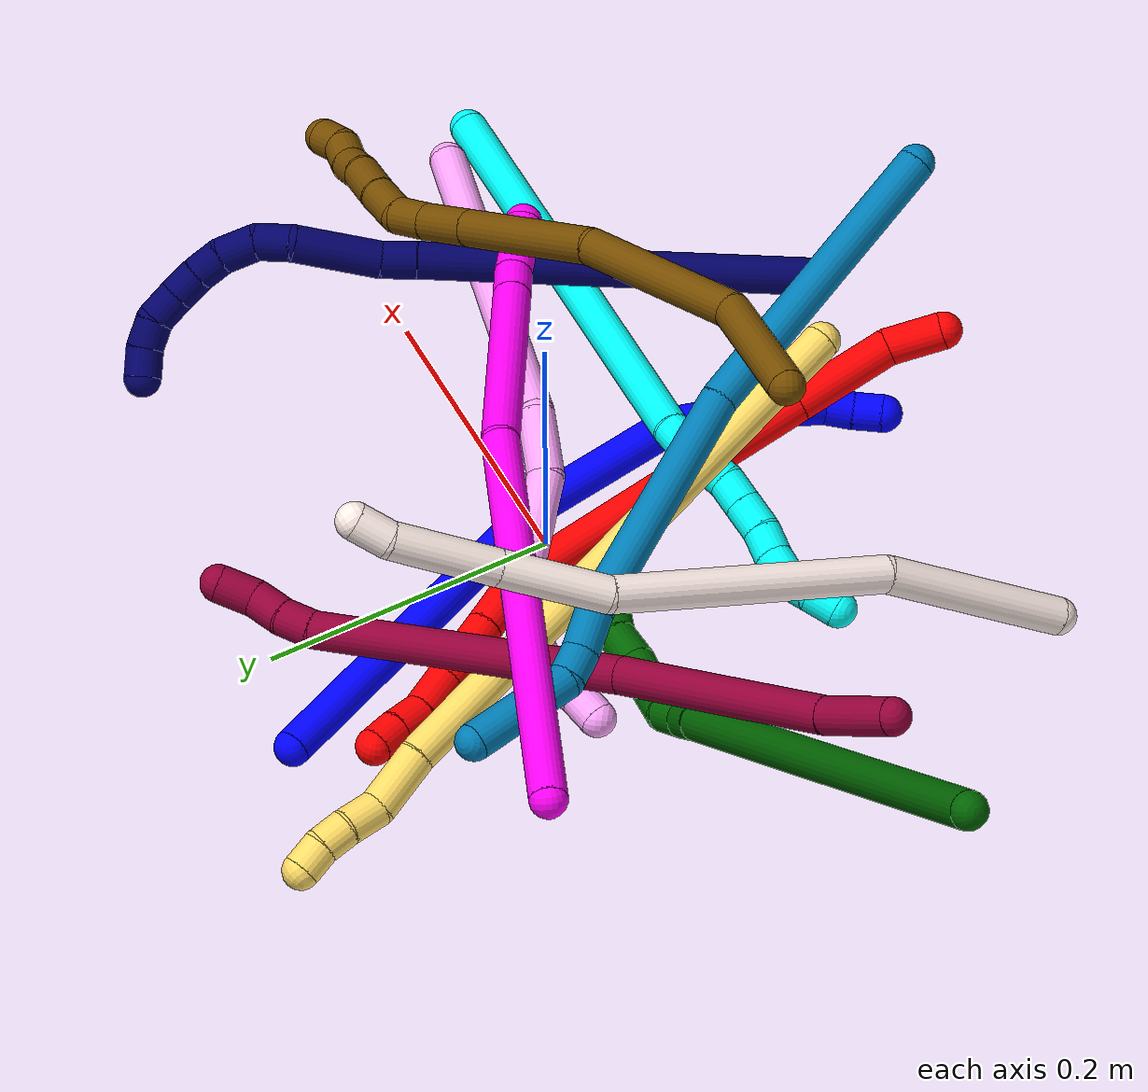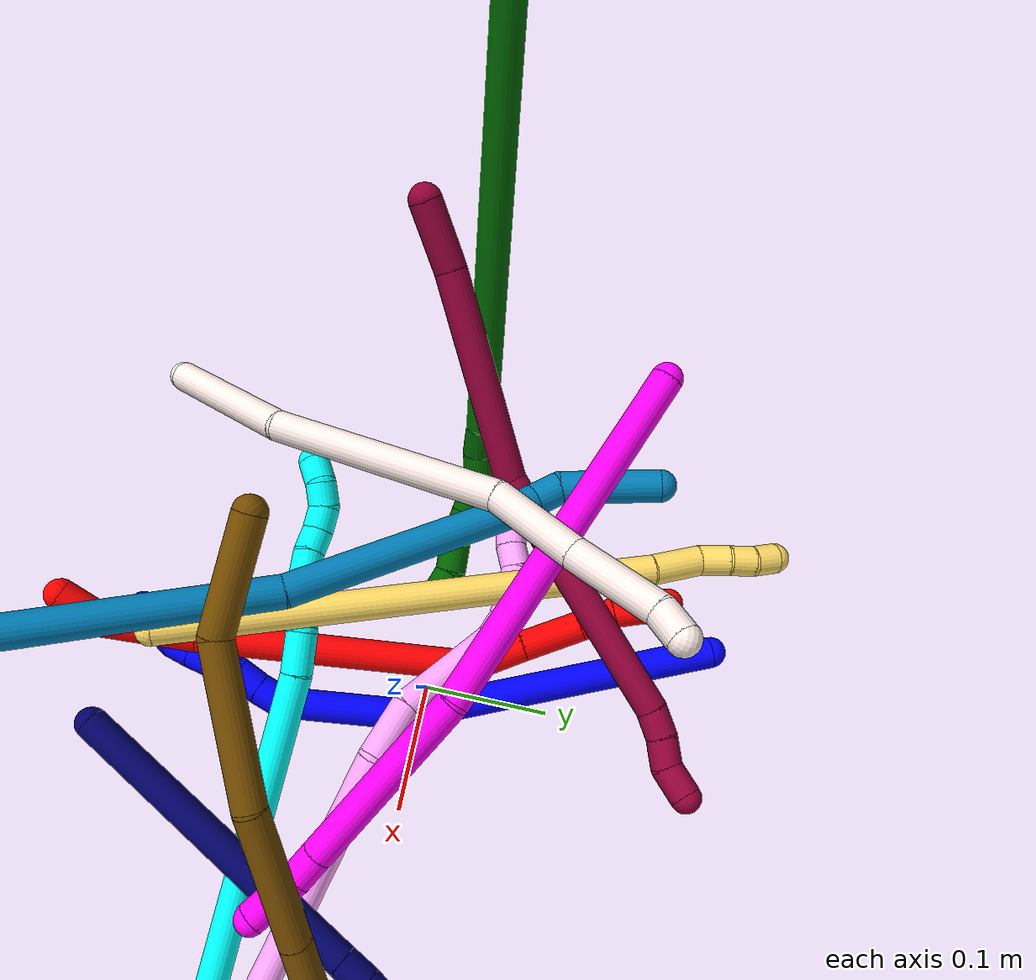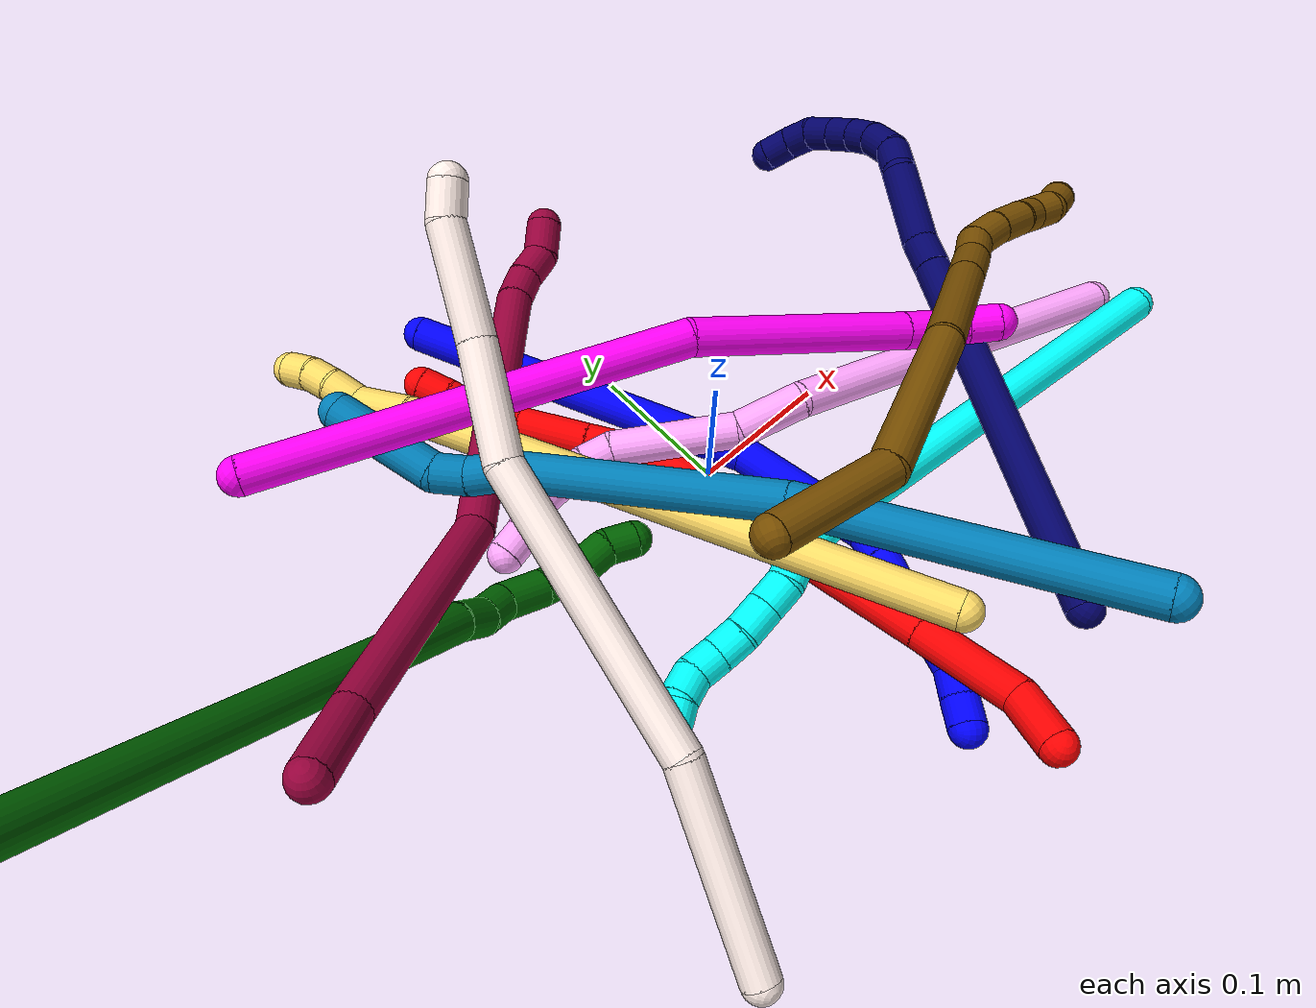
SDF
<sdf version="1.7">
 <world name="default">
  <plugin name="TubeGeneratorPlugin" filename="libtube_generator_plugin.so"/>
  <model name="photoneo_s_sensor">
   <static>1</static>
   <pose>0 0 2 1.57079 1.57079 3.14159</pose>
   <link name="link">
    <inertial><mass>0.1</mass></inertial>
    <sensor name="sensor" type="depth">
     <update_rate>30</update_rate>
     <camera>
      <horizontal_fov>1.22</horizontal_fov>
      <image><width>1920</width><height>1200</height><format>B8G8R8</format></image>
      <clip><near>0.1</near><far>4</far></clip>
      <depth_camera><output>points</output></depth_camera>
     </camera>
     <plugin name="camera_plugin" filename="libgazebo_ros_depth_camera.so">
      <baseline>0.2</baseline>
      <alwaysOn>1</alwaysOn>
      <updateRate>0.0</updateRate>
      <cameraName>camera_ir</cameraName>
      <imageTopicName>/camera/color/image_raw</imageTopicName>
      <cameraInfoTopicName>/camera/color/camera_info</cameraInfoTopicName>
      <depthImageTopicName>/camera/depth/image_raw</depthImageTopicName>
      <depthImageCameraInfoTopicName>/camera/depth/camera_info</depthImageCameraInfoTopicName>
      <pointCloudTopicName>/camera/depth/points</pointCloudTopicName>
      <frameName>fr_optical</frameName>
      <pointCloudCutoff>0.1</pointCloudCutoff>
      <pointCloudCutoffMax>2.0</pointCloudCutoffMax>
      <distortionK1>0</distortionK1>
      <distortionK2>0</distortionK2>
      <distortionK3>0</distortionK3>
      <distortionT1>0</distortionT1>
      <distortionT2>0</distortionT2>
      <CxPrime>0</CxPrime>
      <Cx>0</Cx>
      <Cy>0</Cy>
      <focalLength>0</focalLength>
      <hackBaseline>0</hackBaseline>
     </plugin>
    </sensor>
   </link>
  </model>
  <gravity>0 0 -9.8</gravity>
  <magnetic_field>6e-06 2.3e-05 -4.2e-05</magnetic_field>
  <atmosphere type="adiabatic"/>
  <physics name="default_physics" default="0" type="ode">
   <max_step_size>0.003</max_step_size>
   <real_time_factor>1</real_time_factor>
   <real_time_update_rate>1000</real_time_update_rate>
   <max_contacts>10000</max_contacts>
   <ode>
    <solver>
     <type>quick</type>
     <iters>100</iters>
     <sor>1.3</sor>
     <use_dynamic_moi_rescaling>0</use_dynamic_moi_rescaling>
    </solver>
    <constraints>
     <contact_max_correcting_vel>0</contact_max_correcting_vel>
     <contact_surface_layer>0.001</contact_surface_layer>
     <cfm>0</cfm>
     <erp>0.2</erp>
    </constraints>
   </ode>
  </physics>
  <scene><ambient>0.4 0.4 0.4 1</ambient><background>0.7 0.7 0.7 1</background><shadows>0</shadows></scene>
  <audio><device>default</device></audio>
  <spherical_coordinates>
   <surface_model>EARTH_WGS84</surface_model>
   <latitude_deg>0</latitude_deg>
   <longitude_deg>0</longitude_deg>
   <elevation>0</elevation>
   <heading_deg>0</heading_deg>
  </spherical_coordinates>
  <model name="bin">
   <static>1</static>
   <link name="bottom">
    <collision name="collision-bottom">
     <pose>0 0 -0.01 0 -0 0</pose>
     <geometry><box><size>0.8 0.6 0.02</size></box></geometry>
     <surface>
      <friction><ode><mu>100</mu><mu2>100</mu2></ode></friction>
      <contact><collide_bitmask>65535</collide_bitmask></contact>
     </surface>
    </collision>
   </link>
   <link name="west_wall">
    <collision name="collision-west_wall">
     <pose>-0.41 0 0.1 0 -0 0</pose>
     <geometry><box><size>0.02 0.6 0.2</size></box></geometry>
     <surface>
      <friction><ode><mu>100</mu><mu2>100</mu2></ode></friction>
      <contact><collide_bitmask>65535</collide_bitmask></contact>
     </surface>
    </collision>
   </link>
   <link name="east_wall">
    <collision name="collision-east_wall">
     <pose>0.41 0 0.1 0 -0 0</pose>
     <geometry><box><size>0.02 0.6 0.2</size></box></geometry>
     <surface>
      <friction><ode><mu>100</mu><mu2>100</mu2></ode></friction>
      <contact><collide_bitmask>65535</collide_bitmask></contact>
     </surface>
    </collision>
   </link>
   <link name="south_wall">
    <collision name="collision-south_wall">
     <pose>0 -0.31 0.1 0 -0 0</pose>
     <geometry><box><size>0.8 0.02 0.2</size></box></geometry>
     <surface>
      <friction><ode><mu>100</mu><mu2>100</mu2></ode></friction>
      <contact><collide_bitmask>65535</collide_bitmask></contact>
     </surface>
    </collision>
   </link>
   <link name="north_wall">
    <collision name="collision-north_wall">
     <pose>0 0.31 0.1 0 -0 0</pose>
     <geometry><box><size>0.8 0.02 0.2</size></box></geometry>
     <surface>
      <friction><ode><mu>100</mu><mu2>100</mu2></ode></friction>
      <contact><collide_bitmask>65535</collide_bitmask></contact>
     </surface>
    </collision>
   </link>
  </model>
  <model name="1">
   <static>0</static>
   <link name="1">
    <collision name="collision-cylinder-e_1_1_4">
     <pose>0.044581 -0.08214 -0.085067 2.3737 0.360527 0.84753</pose>
     <geometry><cylinder><radius>0.0125</radius><length>0.252752</length></cylinder></geometry>
     <surface>
      <friction><ode><mu>1.16</mu><mu2>1.16</mu2><slip1>0</slip1><slip2>0</slip2></ode></friction>
      <contact><ode><kp>1e+06</kp><kd>1</kd><max_vel>0</max_vel><min_depth>0.001</min_depth></ode></contact>
     </surface>
    </collision>
    <visual name="visual-cylinder-e_1_1_4">
     <pose>0.044581 -0.08214 -0.085067 2.3737 0.360527 0.84753</pose>
     <geometry><cylinder><radius>0.0125</radius><length>0.252752</length></cylinder></geometry>
     <material><ambient>0 0 1 1</ambient></material>
    </visual>
    <collision name="collision-cylinder-e_2_4_5">
     <pose>0.10799 -0.206264 -0.191586 2.04318 0.379939 0.608849</pose>
     <geometry><cylinder><radius>0.0125</radius><length>0.101533</length></cylinder></geometry>
     <surface>
      <friction><ode><mu>1.16</mu><mu2>1.16</mu2><slip1>0</slip1><slip2>0</slip2></ode></friction>
      <contact><ode><kp>1e+06</kp><kd>1</kd><max_vel>0</max_vel><min_depth>0.001</min_depth></ode></contact>
     </surface>
    </collision>
    <visual name="visual-cylinder-e_2_4_5">
     <pose>0.10799 -0.206264 -0.191586 2.04318 0.379939 0.608849</pose>
     <geometry><cylinder><radius>0.0125</radius><length>0.101533</length></cylinder></geometry>
     <material><ambient>0 0 1 1</ambient></material>
    </visual>
    <collision name="collision-cylinder-e_3_5_6">
     <pose>0.12929 -0.258562 -0.213414 1.60724 0.23504 0.243681</pose>
     <geometry><cylinder><radius>0.0125</radius><length>0.021228</length></cylinder></geometry>
     <surface>
      <friction><ode><mu>1.16</mu><mu2>1.16</mu2><slip1>0</slip1><slip2>0</slip2></ode></friction>
      <contact><ode><kp>1e+06</kp><kd>1</kd><max_vel>0</max_vel><min_depth>0.001</min_depth></ode></contact>
     </surface>
    </collision>
    <visual name="visual-cylinder-e_3_5_6">
     <pose>0.12929 -0.258562 -0.213414 1.60724 0.23504 0.243681</pose>
     <geometry><cylinder><radius>0.0125</radius><length>0.021228</length></cylinder></geometry>
     <material><ambient>0 0 1 1</ambient></material>
    </visual>
    <collision name="collision-cylinder-e_4_6_7">
     <pose>0.134028 -0.279332 -0.213062 1.5012 0.212951 0.198721</pose>
     <geometry><cylinder><radius>0.0125</radius><length>0.021446</length></cylinder></geometry>
     <surface>
      <friction><ode><mu>1.16</mu><mu2>1.16</mu2><slip1>0</slip1><slip2>0</slip2></ode></friction>
      <contact><ode><kp>1e+06</kp><kd>1</kd><max_vel>0</max_vel><min_depth>0.001</min_depth></ode></contact>
     </surface>
    </collision>
    <visual name="visual-cylinder-e_4_6_7">
     <pose>0.134028 -0.279332 -0.213062 1.5012 0.212951 0.198721</pose>
     <geometry><cylinder><radius>0.0125</radius><length>0.021446</length></cylinder></geometry>
     <material><ambient>0 0 1 1</ambient></material>
    </visual>
    <collision name="collision-cylinder-e_5_7_8">
     <pose>0.137877 -0.299781 -0.214802 1.81298 0.152589 0.194634</pose>
     <geometry><cylinder><radius>0.0125</radius><length>0.020829</length></cylinder></geometry>
     <surface>
      <friction><ode><mu>1.16</mu><mu2>1.16</mu2><slip1>0</slip1><slip2>0</slip2></ode></friction>
      <contact><ode><kp>1e+06</kp><kd>1</kd><max_vel>0</max_vel><min_depth>0.001</min_depth></ode></contact>
     </surface>
    </collision>
    <visual name="visual-cylinder-e_5_7_8">
     <pose>0.137877 -0.299781 -0.214802 1.81298 0.152589 0.194634</pose>
     <geometry><cylinder><radius>0.0125</radius><length>0.020829</length></cylinder></geometry>
     <material><ambient>0 0 1 1</ambient></material>
    </visual>
    <collision name="collision-cylinder-e_6_8_9">
     <pose>0.139377 -0.319566 -0.220171 1.85878 -0.008065 -0.010801</pose>
     <geometry><cylinder><radius>0.0125</radius><length>0.020427</length></cylinder></geometry>
     <surface>
      <friction><ode><mu>1.16</mu><mu2>1.16</mu2><slip1>0</slip1><slip2>0</slip2></ode></friction>
      <contact><ode><kp>1e+06</kp><kd>1</kd><max_vel>0</max_vel><min_depth>0.001</min_depth></ode></contact>
     </surface>
    </collision>
    <visual name="visual-cylinder-e_6_8_9">
     <pose>0.139377 -0.319566 -0.220171 1.85878 -0.008065 -0.010801</pose>
     <geometry><cylinder><radius>0.0125</radius><length>0.020427</length></cylinder></geometry>
     <material><ambient>0 0 1 1</ambient></material>
    </visual>
    <collision name="collision-cylinder-e_7_9_10">
     <pose>0.139365 -0.339882 -0.225251 1.77503 0.006524 0.008014</pose>
     <geometry><cylinder><radius>0.0125</radius><length>0.021494</length></cylinder></geometry>
     <surface>
      <friction><ode><mu>1.16</mu><mu2>1.16</mu2><slip1>0</slip1><slip2>0</slip2></ode></friction>
      <contact><ode><kp>1e+06</kp><kd>1</kd><max_vel>0</max_vel><min_depth>0.001</min_depth></ode></contact>
     </surface>
    </collision>
    <visual name="visual-cylinder-e_7_9_10">
     <pose>0.139365 -0.339882 -0.225251 1.77503 0.006524 0.008014</pose>
     <geometry><cylinder><radius>0.0125</radius><length>0.021494</length></cylinder></geometry>
     <material><ambient>0 0 1 1</ambient></material>
    </visual>
    <collision name="collision-cylinder-e_8_10_11">
     <pose>0.138851 -0.360335 -0.225902 1.41799 -0.058051 -0.049799</pose>
     <geometry><cylinder><radius>0.0125</radius><length>0.020127</length></cylinder></geometry>
     <surface>
      <friction><ode><mu>1.16</mu><mu2>1.16</mu2><slip1>0</slip1><slip2>0</slip2></ode></friction>
      <contact><ode><kp>1e+06</kp><kd>1</kd><max_vel>0</max_vel><min_depth>0.001</min_depth></ode></contact>
     </surface>
    </collision>
    <visual name="visual-cylinder-e_8_10_11">
     <pose>0.138851 -0.360335 -0.225902 1.41799 -0.058051 -0.049799</pose>
     <geometry><cylinder><radius>0.0125</radius><length>0.020127</length></cylinder></geometry>
     <material><ambient>0 0 1 1</ambient></material>
    </visual>
    <collision name="collision-cylinder-e_9_11_2">
     <pose>0.139127 -0.380017 -0.221964 1.32874 0.085336 0.066845</pose>
     <geometry><cylinder><radius>0.0125</radius><length>0.020165</length></cylinder></geometry>
     <surface>
      <friction><ode><mu>1.16</mu><mu2>1.16</mu2><slip1>0</slip1><slip2>0</slip2></ode></friction>
      <contact><ode><kp>1e+06</kp><kd>1</kd><max_vel>0</max_vel><min_depth>0.001</min_depth></ode></contact>
     </surface>
    </collision>
    <visual name="visual-cylinder-e_9_11_2">
     <pose>0.139127 -0.380017 -0.221964 1.32874 0.085336 0.066845</pose>
     <geometry><cylinder><radius>0.0125</radius><length>0.020165</length></cylinder></geometry>
     <material><ambient>0 0 1 1</ambient></material>
    </visual>
    <collision name="collision-sphere-2">
     <pose>0.139986 -0.38977 -0.219557 0 -0 0</pose>
     <geometry><sphere><radius>0.0125</radius></sphere></geometry>
     <surface>
      <friction><ode><mu>1.16</mu><mu2>1.16</mu2><slip1>0</slip1><slip2>0</slip2></ode></friction>
      <contact><ode><kp>1e+06</kp><kd>1</kd><max_vel>0</max_vel><min_depth>0.001</min_depth></ode></contact>
     </surface>
    </collision>
    <visual name="visual-sphere-2">
     <pose>0.139986 -0.38977 -0.219557 0 -0 0</pose>
     <geometry><sphere><radius>0.0125</radius></sphere></geometry>
     <material><ambient>0 0 1 1</ambient></material>
    </visual>
    <collision name="collision-sphere-11">
     <pose>0.138268 -0.370264 -0.224372 0 -0 0</pose>
     <geometry><sphere><radius>0.0125</radius></sphere></geometry>
     <surface>
      <friction><ode><mu>1.16</mu><mu2>1.16</mu2><slip1>0</slip1><slip2>0</slip2></ode></friction>
      <contact><ode><kp>1e+06</kp><kd>1</kd><max_vel>0</max_vel><min_depth>0.001</min_depth></ode></contact>
     </surface>
    </collision>
    <visual name="visual-sphere-11">
     <pose>0.138268 -0.370264 -0.224372 0 -0 0</pose>
     <geometry><sphere><radius>0.0125</radius></sphere></geometry>
     <material><ambient>0 0 1 1</ambient></material>
    </visual>
    <collision name="collision-sphere-10">
     <pose>0.139435 -0.350406 -0.227431 0 -0 0</pose>
     <geometry><sphere><radius>0.0125</radius></sphere></geometry>
     <surface>
      <friction><ode><mu>1.16</mu><mu2>1.16</mu2><slip1>0</slip1><slip2>0</slip2></ode></friction>
      <contact><ode><kp>1e+06</kp><kd>1</kd><max_vel>0</max_vel><min_depth>0.001</min_depth></ode></contact>
     </surface>
    </collision>
    <visual name="visual-sphere-10">
     <pose>0.139435 -0.350406 -0.227431 0 -0 0</pose>
     <geometry><sphere><radius>0.0125</radius></sphere></geometry>
     <material><ambient>0 0 1 1</ambient></material>
    </visual>
    <collision name="collision-sphere-9">
     <pose>0.139295 -0.329359 -0.223072 0 -0 0</pose>
     <geometry><sphere><radius>0.0125</radius></sphere></geometry>
     <surface>
      <friction><ode><mu>1.16</mu><mu2>1.16</mu2><slip1>0</slip1><slip2>0</slip2></ode></friction>
      <contact><ode><kp>1e+06</kp><kd>1</kd><max_vel>0</max_vel><min_depth>0.001</min_depth></ode></contact>
     </surface>
    </collision>
    <visual name="visual-sphere-9">
     <pose>0.139295 -0.329359 -0.223072 0 -0 0</pose>
     <geometry><sphere><radius>0.0125</radius></sphere></geometry>
     <material><ambient>0 0 1 1</ambient></material>
    </visual>
    <collision name="collision-sphere-4">
     <pose>0.089163 -0.16428 -0.170134 0 -0 0</pose>
     <geometry><sphere><radius>0.0125</radius></sphere></geometry>
     <surface>
      <friction><ode><mu>1.16</mu><mu2>1.16</mu2><slip1>0</slip1><slip2>0</slip2></ode></friction>
      <contact><ode><kp>1e+06</kp><kd>1</kd><max_vel>0</max_vel><min_depth>0.001</min_depth></ode></contact>
     </surface>
    </collision>
    <visual name="visual-sphere-4">
     <pose>0.089163 -0.16428 -0.170134 0 -0 0</pose>
     <geometry><sphere><radius>0.0125</radius></sphere></geometry>
     <material><ambient>0 0 1 1</ambient></material>
    </visual>
    <collision name="collision-sphere-1">
     <geometry><sphere><radius>0.0125</radius></sphere></geometry>
     <surface>
      <friction><ode><mu>1.16</mu><mu2>1.16</mu2><slip1>0</slip1><slip2>0</slip2></ode></friction>
      <contact><ode><kp>1e+06</kp><kd>1</kd><max_vel>0</max_vel><min_depth>0.001</min_depth></ode></contact>
     </surface>
    </collision>
    <visual name="visual-sphere-1">
     <geometry><sphere><radius>0.0125</radius></sphere></geometry>
     <material><ambient>0 0 1 1</ambient></material>
    </visual>
    <collision name="collision-sphere-8">
     <pose>0.13946 -0.309774 -0.21727 0 -0 0</pose>
     <geometry><sphere><radius>0.0125</radius></sphere></geometry>
     <surface>
      <friction><ode><mu>1.16</mu><mu2>1.16</mu2><slip1>0</slip1><slip2>0</slip2></ode></friction>
      <contact><ode><kp>1e+06</kp><kd>1</kd><max_vel>0</max_vel><min_depth>0.001</min_depth></ode></contact>
     </surface>
    </collision>
    <visual name="visual-sphere-8">
     <pose>0.13946 -0.309774 -0.21727 0 -0 0</pose>
     <geometry><sphere><radius>0.0125</radius></sphere></geometry>
     <material><ambient>0 0 1 1</ambient></material>
    </visual>
    <collision name="collision-sphere-5">
     <pose>0.126818 -0.248247 -0.213038 0 -0 0</pose>
     <geometry><sphere><radius>0.0125</radius></sphere></geometry>
     <surface>
      <friction><ode><mu>1.16</mu><mu2>1.16</mu2><slip1>0</slip1><slip2>0</slip2></ode></friction>
      <contact><ode><kp>1e+06</kp><kd>1</kd><max_vel>0</max_vel><min_depth>0.001</min_depth></ode></contact>
     </surface>
    </collision>
    <visual name="visual-sphere-5">
     <pose>0.126818 -0.248247 -0.213038 0 -0 0</pose>
     <geometry><sphere><radius>0.0125</radius></sphere></geometry>
     <material><ambient>0 0 1 1</ambient></material>
    </visual>
    <collision name="collision-sphere-6">
     <pose>0.131761 -0.268877 -0.21379 0 -0 0</pose>
     <geometry><sphere><radius>0.0125</radius></sphere></geometry>
     <surface>
      <friction><ode><mu>1.16</mu><mu2>1.16</mu2><slip1>0</slip1><slip2>0</slip2></ode></friction>
      <contact><ode><kp>1e+06</kp><kd>1</kd><max_vel>0</max_vel><min_depth>0.001</min_depth></ode></contact>
     </surface>
    </collision>
    <visual name="visual-sphere-6">
     <pose>0.131761 -0.268877 -0.21379 0 -0 0</pose>
     <geometry><sphere><radius>0.0125</radius></sphere></geometry>
     <material><ambient>0 0 1 1</ambient></material>
    </visual>
    <collision name="collision-sphere-7">
     <pose>0.136294 -0.289788 -0.212333 0 -0 0</pose>
     <geometry><sphere><radius>0.0125</radius></sphere></geometry>
     <surface>
      <friction><ode><mu>1.16</mu><mu2>1.16</mu2><slip1>0</slip1><slip2>0</slip2></ode></friction>
      <contact><ode><kp>1e+06</kp><kd>1</kd><max_vel>0</max_vel><min_depth>0.001</min_depth></ode></contact>
     </surface>
    </collision>
    <visual name="visual-sphere-7">
     <pose>0.136294 -0.289788 -0.212333 0 -0 0</pose>
     <geometry><sphere><radius>0.0125</radius></sphere></geometry>
     <material><ambient>0 0 1 1</ambient></material>
    </visual>
    <inertial>
     <pose>0.084332 -0.176351 -0.145777 0 -0 0</pose>
     <mass>0.5</mass>
     <inertia>
      <ixx>0.001931</ixx>
      <ixy>0</ixy>
      <ixz>0</ixz>
      <iyy>0.000556</iyy>
      <iyz>0</iyz>
      <izz>0.000437</izz>
     </inertia>
    </inertial>
   </link>
   <pose>-0.077087 0.222004 0.012069 0.311799 -1.16614 -0.734313</pose>
  </model>
  <model name="2">
   <static>0</static>
   <link name="2">
    <collision name="collision-cylinder-e_1_1_4">
     <pose>-0.012737 0.011349 0.009053 -0.897487 -0.720167 0.358677</pose>
     <geometry><cylinder><radius>0.0125</radius><length>0.038627</length></cylinder></geometry>
     <surface>
      <friction><ode><mu>1.16</mu><mu2>1.16</mu2><slip1>0</slip1><slip2>0</slip2></ode></friction>
      <contact><ode><kp>1e+06</kp><kd>1</kd><max_vel>0</max_vel><min_depth>0.001</min_depth></ode></contact>
     </surface>
    </collision>
    <visual name="visual-cylinder-e_1_1_4">
     <pose>-0.012737 0.011349 0.009053 -0.897487 -0.720167 0.358677</pose>
     <geometry><cylinder><radius>0.0125</radius><length>0.038627</length></cylinder></geometry>
     <material><ambient>1 0 0 1</ambient></material>
    </visual>
    <collision name="collision-cylinder-e_2_4_5">
     <pose>-0.037715 0.05317 0.031824 -1.14779 -0.351125 0.228357</pose>
     <geometry><cylinder><radius>0.0125</radius><length>0.071175</length></cylinder></geometry>
     <surface>
      <friction><ode><mu>1.16</mu><mu2>1.16</mu2><slip1>0</slip1><slip2>0</slip2></ode></friction>
      <contact><ode><kp>1e+06</kp><kd>1</kd><max_vel>0</max_vel><min_depth>0.001</min_depth></ode></contact>
     </surface>
    </collision>
    <visual name="visual-cylinder-e_2_4_5">
     <pose>-0.037715 0.05317 0.031824 -1.14779 -0.351125 0.228357</pose>
     <geometry><cylinder><radius>0.0125</radius><length>0.071175</length></cylinder></geometry>
     <material><ambient>1 0 0 1</ambient></material>
    </visual>
    <collision name="collision-cylinder-e_3_5_6">
     <pose>-0.083503 0.183421 0.079303 -1.24453 -0.308321 0.222022</pose>
     <geometry><cylinder><radius>0.0125</radius><length>0.221101</length></cylinder></geometry>
     <surface>
      <friction><ode><mu>1.16</mu><mu2>1.16</mu2><slip1>0</slip1><slip2>0</slip2></ode></friction>
      <contact><ode><kp>1e+06</kp><kd>1</kd><max_vel>0</max_vel><min_depth>0.001</min_depth></ode></contact>
     </surface>
    </collision>
    <visual name="visual-cylinder-e_3_5_6">
     <pose>-0.083503 0.183421 0.079303 -1.24453 -0.308321 0.222022</pose>
     <geometry><cylinder><radius>0.0125</radius><length>0.221101</length></cylinder></geometry>
     <material><ambient>1 0 0 1</ambient></material>
    </visual>
    <collision name="collision-cylinder-e_4_6_7">
     <pose>-0.113929 0.305263 0.116078 -1.43505 0.139301 -0.121615</pose>
     <geometry><cylinder><radius>0.0125</radius><length>0.044967</length></cylinder></geometry>
     <surface>
      <friction><ode><mu>1.16</mu><mu2>1.16</mu2><slip1>0</slip1><slip2>0</slip2></ode></friction>
      <contact><ode><kp>1e+06</kp><kd>1</kd><max_vel>0</max_vel><min_depth>0.001</min_depth></ode></contact>
     </surface>
    </collision>
    <visual name="visual-cylinder-e_4_6_7">
     <pose>-0.113929 0.305263 0.116078 -1.43505 0.139301 -0.121615</pose>
     <geometry><cylinder><radius>0.0125</radius><length>0.044967</length></cylinder></geometry>
     <material><ambient>1 0 0 1</ambient></material>
    </visual>
    <collision name="collision-cylinder-e_5_7_8">
     <pose>-0.107932 0.351562 0.1229 -1.41492 0.116663 -0.099792</pose>
     <geometry><cylinder><radius>0.0125</radius><length>0.049408</length></cylinder></geometry>
     <surface>
      <friction><ode><mu>1.16</mu><mu2>1.16</mu2><slip1>0</slip1><slip2>0</slip2></ode></friction>
      <contact><ode><kp>1e+06</kp><kd>1</kd><max_vel>0</max_vel><min_depth>0.001</min_depth></ode></contact>
     </surface>
    </collision>
    <visual name="visual-cylinder-e_5_7_8">
     <pose>-0.107932 0.351562 0.1229 -1.41492 0.116663 -0.099792</pose>
     <geometry><cylinder><radius>0.0125</radius><length>0.049408</length></cylinder></geometry>
     <material><ambient>1 0 0 1</ambient></material>
    </visual>
    <collision name="collision-cylinder-e_6_8_9">
     <pose>-0.102842 0.391097 0.127942 -1.49038 0.143307 -0.132256</pose>
     <geometry><cylinder><radius>0.0125</radius><length>0.03101</length></cylinder></geometry>
     <surface>
      <friction><ode><mu>1.16</mu><mu2>1.16</mu2><slip1>0</slip1><slip2>0</slip2></ode></friction>
      <contact><ode><kp>1e+06</kp><kd>1</kd><max_vel>0</max_vel><min_depth>0.001</min_depth></ode></contact>
     </surface>
    </collision>
    <visual name="visual-cylinder-e_6_8_9">
     <pose>-0.102842 0.391097 0.127942 -1.49038 0.143307 -0.132256</pose>
     <geometry><cylinder><radius>0.0125</radius><length>0.03101</length></cylinder></geometry>
     <material><ambient>1 0 0 1</ambient></material>
    </visual>
    <collision name="collision-cylinder-e_7_9_10">
     <pose>-0.101893 0.418 0.128937 -1.59125 -0.108552 0.110791</pose>
     <geometry><cylinder><radius>0.0125</radius><length>0.023355</length></cylinder></geometry>
     <surface>
      <friction><ode><mu>1.16</mu><mu2>1.16</mu2><slip1>0</slip1><slip2>0</slip2></ode></friction>
      <contact><ode><kp>1e+06</kp><kd>1</kd><max_vel>0</max_vel><min_depth>0.001</min_depth></ode></contact>
     </surface>
    </collision>
    <visual name="visual-cylinder-e_7_9_10">
     <pose>-0.101893 0.418 0.128937 -1.59125 -0.108552 0.110791</pose>
     <geometry><cylinder><radius>0.0125</radius><length>0.023355</length></cylinder></geometry>
     <material><ambient>1 0 0 1</ambient></material>
    </visual>
    <collision name="collision-cylinder-e_8_10_2">
     <pose>-0.103542 0.43977 0.12908 -1.53338 -0.037702 0.036317</pose>
     <geometry><cylinder><radius>0.0125</radius><length>0.020357</length></cylinder></geometry>
     <surface>
      <friction><ode><mu>1.16</mu><mu2>1.16</mu2><slip1>0</slip1><slip2>0</slip2></ode></friction>
      <contact><ode><kp>1e+06</kp><kd>1</kd><max_vel>0</max_vel><min_depth>0.001</min_depth></ode></contact>
     </surface>
    </collision>
    <visual name="visual-cylinder-e_8_10_2">
     <pose>-0.103542 0.43977 0.12908 -1.53338 -0.037702 0.036317</pose>
     <geometry><cylinder><radius>0.0125</radius><length>0.020357</length></cylinder></geometry>
     <material><ambient>1 0 0 1</ambient></material>
    </visual>
    <collision name="collision-sphere-2">
     <pose>-0.103925 0.449934 0.129461 0 -0 0</pose>
     <geometry><sphere><radius>0.0125</radius></sphere></geometry>
     <surface>
      <friction><ode><mu>1.16</mu><mu2>1.16</mu2><slip1>0</slip1><slip2>0</slip2></ode></friction>
      <contact><ode><kp>1e+06</kp><kd>1</kd><max_vel>0</max_vel><min_depth>0.001</min_depth></ode></contact>
     </surface>
    </collision>
    <visual name="visual-sphere-2">
     <pose>-0.103925 0.449934 0.129461 0 -0 0</pose>
     <geometry><sphere><radius>0.0125</radius></sphere></geometry>
     <material><ambient>1 0 0 1</ambient></material>
    </visual>
    <collision name="collision-sphere-10">
     <pose>-0.103158 0.429606 0.1287 0 -0 0</pose>
     <geometry><sphere><radius>0.0125</radius></sphere></geometry>
     <surface>
      <friction><ode><mu>1.16</mu><mu2>1.16</mu2><slip1>0</slip1><slip2>0</slip2></ode></friction>
      <contact><ode><kp>1e+06</kp><kd>1</kd><max_vel>0</max_vel><min_depth>0.001</min_depth></ode></contact>
     </surface>
    </collision>
    <visual name="visual-sphere-10">
     <pose>-0.103158 0.429606 0.1287 0 -0 0</pose>
     <geometry><sphere><radius>0.0125</radius></sphere></geometry>
     <material><ambient>1 0 0 1</ambient></material>
    </visual>
    <collision name="collision-sphere-9">
     <pose>-0.100628 0.406393 0.129174 0 -0 0</pose>
     <geometry><sphere><radius>0.0125</radius></sphere></geometry>
     <surface>
      <friction><ode><mu>1.16</mu><mu2>1.16</mu2><slip1>0</slip1><slip2>0</slip2></ode></friction>
      <contact><ode><kp>1e+06</kp><kd>1</kd><max_vel>0</max_vel><min_depth>0.001</min_depth></ode></contact>
     </surface>
    </collision>
    <visual name="visual-sphere-9">
     <pose>-0.100628 0.406393 0.129174 0 -0 0</pose>
     <geometry><sphere><radius>0.0125</radius></sphere></geometry>
     <material><ambient>1 0 0 1</ambient></material>
    </visual>
    <collision name="collision-sphere-4">
     <pose>-0.025475 0.022699 0.018106 0 -0 0</pose>
     <geometry><sphere><radius>0.0125</radius></sphere></geometry>
     <surface>
      <friction><ode><mu>1.16</mu><mu2>1.16</mu2><slip1>0</slip1><slip2>0</slip2></ode></friction>
      <contact><ode><kp>1e+06</kp><kd>1</kd><max_vel>0</max_vel><min_depth>0.001</min_depth></ode></contact>
     </surface>
    </collision>
    <visual name="visual-sphere-4">
     <pose>-0.025475 0.022699 0.018106 0 -0 0</pose>
     <geometry><sphere><radius>0.0125</radius></sphere></geometry>
     <material><ambient>1 0 0 1</ambient></material>
    </visual>
    <collision name="collision-sphere-1">
     <geometry><sphere><radius>0.0125</radius></sphere></geometry>
     <surface>
      <friction><ode><mu>1.16</mu><mu2>1.16</mu2><slip1>0</slip1><slip2>0</slip2></ode></friction>
      <contact><ode><kp>1e+06</kp><kd>1</kd><max_vel>0</max_vel><min_depth>0.001</min_depth></ode></contact>
     </surface>
    </collision>
    <visual name="visual-sphere-1">
     <geometry><sphere><radius>0.0125</radius></sphere></geometry>
     <material><ambient>1 0 0 1</ambient></material>
    </visual>
    <collision name="collision-sphere-8">
     <pose>-0.105056 0.375801 0.126709 0 -0 0</pose>
     <geometry><sphere><radius>0.0125</radius></sphere></geometry>
     <surface>
      <friction><ode><mu>1.16</mu><mu2>1.16</mu2><slip1>0</slip1><slip2>0</slip2></ode></friction>
      <contact><ode><kp>1e+06</kp><kd>1</kd><max_vel>0</max_vel><min_depth>0.001</min_depth></ode></contact>
     </surface>
    </collision>
    <visual name="visual-sphere-8">
     <pose>-0.105056 0.375801 0.126709 0 -0 0</pose>
     <geometry><sphere><radius>0.0125</radius></sphere></geometry>
     <material><ambient>1 0 0 1</ambient></material>
    </visual>
    <collision name="collision-sphere-5">
     <pose>-0.049956 0.083641 0.045541 0 -0 0</pose>
     <geometry><sphere><radius>0.0125</radius></sphere></geometry>
     <surface>
      <friction><ode><mu>1.16</mu><mu2>1.16</mu2><slip1>0</slip1><slip2>0</slip2></ode></friction>
      <contact><ode><kp>1e+06</kp><kd>1</kd><max_vel>0</max_vel><min_depth>0.001</min_depth></ode></contact>
     </surface>
    </collision>
    <visual name="visual-sphere-5">
     <pose>-0.049956 0.083641 0.045541 0 -0 0</pose>
     <geometry><sphere><radius>0.0125</radius></sphere></geometry>
     <material><ambient>1 0 0 1</ambient></material>
    </visual>
    <collision name="collision-sphere-6">
     <pose>-0.117051 0.283202 0.113064 0 -0 0</pose>
     <geometry><sphere><radius>0.0125</radius></sphere></geometry>
     <surface>
      <friction><ode><mu>1.16</mu><mu2>1.16</mu2><slip1>0</slip1><slip2>0</slip2></ode></friction>
      <contact><ode><kp>1e+06</kp><kd>1</kd><max_vel>0</max_vel><min_depth>0.001</min_depth></ode></contact>
     </surface>
    </collision>
    <visual name="visual-sphere-6">
     <pose>-0.117051 0.283202 0.113064 0 -0 0</pose>
     <geometry><sphere><radius>0.0125</radius></sphere></geometry>
     <material><ambient>1 0 0 1</ambient></material>
    </visual>
    <collision name="collision-sphere-7">
     <pose>-0.110807 0.327324 0.119091 0 -0 0</pose>
     <geometry><sphere><radius>0.0125</radius></sphere></geometry>
     <surface>
      <friction><ode><mu>1.16</mu><mu2>1.16</mu2><slip1>0</slip1><slip2>0</slip2></ode></friction>
      <contact><ode><kp>1e+06</kp><kd>1</kd><max_vel>0</max_vel><min_depth>0.001</min_depth></ode></contact>
     </surface>
    </collision>
    <visual name="visual-sphere-7">
     <pose>-0.110807 0.327324 0.119091 0 -0 0</pose>
     <geometry><sphere><radius>0.0125</radius></sphere></geometry>
     <material><ambient>1 0 0 1</ambient></material>
    </visual>
    <inertial>
     <pose>-0.079543 0.213434 0.082094 0 -0 0</pose>
     <mass>0.5</mass>
     <inertia>
      <ixx>0.001097</ixx>
      <ixy>0</ixy>
      <ixz>0</ixz>
      <iyy>0.000598</iyy>
      <iyz>0</iyz>
      <izz>-0.000582</izz>
     </inertia>
    </inertial>
   </link>
   <pose>-0.010267 -0.288507 0.066457 2.96966 0.067006 -2.70989</pose>
  </model>
  <model name="3">
   <static>0</static>
   <link name="3">
    <collision name="collision-cylinder-e_1_1_4">
     <pose>-0.083306 -0.014237 -0.136556 3.03771 -0.545378 -2.77399</pose>
     <geometry><cylinder><radius>0.0125</radius><length>0.321186</length></cylinder></geometry>
     <surface>
      <friction><ode><mu>1.16</mu><mu2>1.16</mu2><slip1>0</slip1><slip2>0</slip2></ode></friction>
      <contact><ode><kp>1e+06</kp><kd>1</kd><max_vel>0</max_vel><min_depth>0.001</min_depth></ode></contact>
     </surface>
    </collision>
    <visual name="visual-cylinder-e_1_1_4">
     <pose>-0.083306 -0.014237 -0.136556 3.03771 -0.545378 -2.77399</pose>
     <geometry><cylinder><radius>0.0125</radius><length>0.321186</length></cylinder></geometry>
     <material><ambient>0.003922 1 0.996078 1</ambient></material>
    </visual>
    <collision name="collision-cylinder-e_2_4_5">
     <pose>-0.173699 -0.028169 -0.28828 -3.12145 -0.43697 3.05093</pose>
     <geometry><cylinder><radius>0.0125</radius><length>0.033489</length></cylinder></geometry>
     <surface>
      <friction><ode><mu>1.16</mu><mu2>1.16</mu2><slip1>0</slip1><slip2>0</slip2></ode></friction>
      <contact><ode><kp>1e+06</kp><kd>1</kd><max_vel>0</max_vel><min_depth>0.001</min_depth></ode></contact>
     </surface>
    </collision>
    <visual name="visual-cylinder-e_2_4_5">
     <pose>-0.173699 -0.028169 -0.28828 -3.12145 -0.43697 3.05093</pose>
     <geometry><cylinder><radius>0.0125</radius><length>0.033489</length></cylinder></geometry>
     <material><ambient>0.003922 1 0.996078 1</ambient></material>
    </visual>
    <collision name="collision-cylinder-e_3_5_6">
     <pose>-0.183757 -0.024209 -0.313811 -2.80262 -0.264176 1.32035</pose>
     <geometry><cylinder><radius>0.0125</radius><length>0.022766</length></cylinder></geometry>
     <surface>
      <friction><ode><mu>1.16</mu><mu2>1.16</mu2><slip1>0</slip1><slip2>0</slip2></ode></friction>
      <contact><ode><kp>1e+06</kp><kd>1</kd><max_vel>0</max_vel><min_depth>0.001</min_depth></ode></contact>
     </surface>
    </collision>
    <visual name="visual-cylinder-e_3_5_6">
     <pose>-0.183757 -0.024209 -0.313811 -2.80262 -0.264176 1.32035</pose>
     <geometry><cylinder><radius>0.0125</radius><length>0.022766</length></cylinder></geometry>
     <material><ambient>0.003922 1 0.996078 1</ambient></material>
    </visual>
    <collision name="collision-cylinder-e_4_6_7">
     <pose>-0.191938 -0.018151 -0.33245 -2.85885 -0.543571 2.19726</pose>
     <geometry><cylinder><radius>0.0125</radius><length>0.02014</length></cylinder></geometry>
     <surface>
      <friction><ode><mu>1.16</mu><mu2>1.16</mu2><slip1>0</slip1><slip2>0</slip2></ode></friction>
      <contact><ode><kp>1e+06</kp><kd>1</kd><max_vel>0</max_vel><min_depth>0.001</min_depth></ode></contact>
     </surface>
    </collision>
    <visual name="visual-cylinder-e_4_6_7">
     <pose>-0.191938 -0.018151 -0.33245 -2.85885 -0.543571 2.19726</pose>
     <geometry><cylinder><radius>0.0125</radius><length>0.02014</length></cylinder></geometry>
     <material><ambient>0.003922 1 0.996078 1</ambient></material>
    </visual>
    <collision name="collision-cylinder-e_5_7_8">
     <pose>-0.202737 -0.013232 -0.349791 -2.87103 -0.536291 2.22171</pose>
     <geometry><cylinder><radius>0.0125</radius><length>0.021887</length></cylinder></geometry>
     <surface>
      <friction><ode><mu>1.16</mu><mu2>1.16</mu2><slip1>0</slip1><slip2>0</slip2></ode></friction>
      <contact><ode><kp>1e+06</kp><kd>1</kd><max_vel>0</max_vel><min_depth>0.001</min_depth></ode></contact>
     </surface>
    </collision>
    <visual name="visual-cylinder-e_5_7_8">
     <pose>-0.202737 -0.013232 -0.349791 -2.87103 -0.536291 2.22171</pose>
     <geometry><cylinder><radius>0.0125</radius><length>0.021887</length></cylinder></geometry>
     <material><ambient>0.003922 1 0.996078 1</ambient></material>
    </visual>
    <collision name="collision-cylinder-e_6_8_9">
     <pose>-0.215035 -0.008414 -0.366074 -2.83265 -0.724563 2.36195</pose>
     <geometry><cylinder><radius>0.0125</radius><length>0.020237</length></cylinder></geometry>
     <surface>
      <friction><ode><mu>1.16</mu><mu2>1.16</mu2><slip1>0</slip1><slip2>0</slip2></ode></friction>
      <contact><ode><kp>1e+06</kp><kd>1</kd><max_vel>0</max_vel><min_depth>0.001</min_depth></ode></contact>
     </surface>
    </collision>
    <visual name="visual-cylinder-e_6_8_9">
     <pose>-0.215035 -0.008414 -0.366074 -2.83265 -0.724563 2.36195</pose>
     <geometry><cylinder><radius>0.0125</radius><length>0.020237</length></cylinder></geometry>
     <material><ambient>0.003922 1 0.996078 1</ambient></material>
    </visual>
    <collision name="collision-cylinder-e_7_9_10">
     <pose>-0.227236 -0.006083 -0.381767 -3.13831 -0.57514 3.13048</pose>
     <geometry><cylinder><radius>0.0125</radius><length>0.020201</length></cylinder></geometry>
     <surface>
      <friction><ode><mu>1.16</mu><mu2>1.16</mu2><slip1>0</slip1><slip2>0</slip2></ode></friction>
      <contact><ode><kp>1e+06</kp><kd>1</kd><max_vel>0</max_vel><min_depth>0.001</min_depth></ode></contact>
     </surface>
    </collision>
    <visual name="visual-cylinder-e_7_9_10">
     <pose>-0.227236 -0.006083 -0.381767 -3.13831 -0.57514 3.13048</pose>
     <geometry><cylinder><radius>0.0125</radius><length>0.020201</length></cylinder></geometry>
     <material><ambient>0.003922 1 0.996078 1</ambient></material>
    </visual>
    <collision name="collision-cylinder-e_8_10_11">
     <pose>-0.23445 -0.005427 -0.400118 -3.07804 -0.17211 2.43554</pose>
     <geometry><cylinder><radius>0.0125</radius><length>0.020089</length></cylinder></geometry>
     <surface>
      <friction><ode><mu>1.16</mu><mu2>1.16</mu2><slip1>0</slip1><slip2>0</slip2></ode></friction>
      <contact><ode><kp>1e+06</kp><kd>1</kd><max_vel>0</max_vel><min_depth>0.001</min_depth></ode></contact>
     </surface>
    </collision>
    <visual name="visual-cylinder-e_8_10_11">
     <pose>-0.23445 -0.005427 -0.400118 -3.07804 -0.17211 2.43554</pose>
     <geometry><cylinder><radius>0.0125</radius><length>0.020089</length></cylinder></geometry>
     <material><ambient>0.003922 1 0.996078 1</ambient></material>
    </visual>
    <collision name="collision-cylinder-e_9_11_2">
     <pose>-0.237264 -0.00054 -0.41898 -2.69905 -0.109509 0.477984</pose>
     <geometry><cylinder><radius>0.0125</radius><length>0.020005</length></cylinder></geometry>
     <surface>
      <friction><ode><mu>1.16</mu><mu2>1.16</mu2><slip1>0</slip1><slip2>0</slip2></ode></friction>
      <contact><ode><kp>1e+06</kp><kd>1</kd><max_vel>0</max_vel><min_depth>0.001</min_depth></ode></contact>
     </surface>
    </collision>
    <visual name="visual-cylinder-e_9_11_2">
     <pose>-0.237264 -0.00054 -0.41898 -2.69905 -0.109509 0.477984</pose>
     <geometry><cylinder><radius>0.0125</radius><length>0.020005</length></cylinder></geometry>
     <material><ambient>0.003922 1 0.996078 1</ambient></material>
    </visual>
    <collision name="collision-sphere-2">
     <pose>-0.238357 0.003718 -0.427965 0 -0 0</pose>
     <geometry><sphere><radius>0.0125</radius></sphere></geometry>
     <surface>
      <friction><ode><mu>1.16</mu><mu2>1.16</mu2><slip1>0</slip1><slip2>0</slip2></ode></friction>
      <contact><ode><kp>1e+06</kp><kd>1</kd><max_vel>0</max_vel><min_depth>0.001</min_depth></ode></contact>
     </surface>
    </collision>
    <visual name="visual-sphere-2">
     <pose>-0.238357 0.003718 -0.427965 0 -0 0</pose>
     <geometry><sphere><radius>0.0125</radius></sphere></geometry>
     <material><ambient>0.003922 1 0.996078 1</ambient></material>
    </visual>
    <collision name="collision-sphere-11">
     <pose>-0.236171 -0.004798 -0.409995 0 -0 0</pose>
     <geometry><sphere><radius>0.0125</radius></sphere></geometry>
     <surface>
      <friction><ode><mu>1.16</mu><mu2>1.16</mu2><slip1>0</slip1><slip2>0</slip2></ode></friction>
      <contact><ode><kp>1e+06</kp><kd>1</kd><max_vel>0</max_vel><min_depth>0.001</min_depth></ode></contact>
     </surface>
    </collision>
    <visual name="visual-sphere-11">
     <pose>-0.236171 -0.004798 -0.409995 0 -0 0</pose>
     <geometry><sphere><radius>0.0125</radius></sphere></geometry>
     <material><ambient>0.003922 1 0.996078 1</ambient></material>
    </visual>
    <collision name="collision-sphere-10">
     <pose>-0.23273 -0.006055 -0.390242 0 -0 0</pose>
     <geometry><sphere><radius>0.0125</radius></sphere></geometry>
     <surface>
      <friction><ode><mu>1.16</mu><mu2>1.16</mu2><slip1>0</slip1><slip2>0</slip2></ode></friction>
      <contact><ode><kp>1e+06</kp><kd>1</kd><max_vel>0</max_vel><min_depth>0.001</min_depth></ode></contact>
     </surface>
    </collision>
    <visual name="visual-sphere-10">
     <pose>-0.23273 -0.006055 -0.390242 0 -0 0</pose>
     <geometry><sphere><radius>0.0125</radius></sphere></geometry>
     <material><ambient>0.003922 1 0.996078 1</ambient></material>
    </visual>
    <collision name="collision-sphere-9">
     <pose>-0.221742 -0.006111 -0.373292 0 -0 0</pose>
     <geometry><sphere><radius>0.0125</radius></sphere></geometry>
     <surface>
      <friction><ode><mu>1.16</mu><mu2>1.16</mu2><slip1>0</slip1><slip2>0</slip2></ode></friction>
      <contact><ode><kp>1e+06</kp><kd>1</kd><max_vel>0</max_vel><min_depth>0.001</min_depth></ode></contact>
     </surface>
    </collision>
    <visual name="visual-sphere-9">
     <pose>-0.221742 -0.006111 -0.373292 0 -0 0</pose>
     <geometry><sphere><radius>0.0125</radius></sphere></geometry>
     <material><ambient>0.003922 1 0.996078 1</ambient></material>
    </visual>
    <collision name="collision-sphere-4">
     <pose>-0.166613 -0.028474 -0.273112 0 -0 0</pose>
     <geometry><sphere><radius>0.0125</radius></sphere></geometry>
     <surface>
      <friction><ode><mu>1.16</mu><mu2>1.16</mu2><slip1>0</slip1><slip2>0</slip2></ode></friction>
      <contact><ode><kp>1e+06</kp><kd>1</kd><max_vel>0</max_vel><min_depth>0.001</min_depth></ode></contact>
     </surface>
    </collision>
    <visual name="visual-sphere-4">
     <pose>-0.166613 -0.028474 -0.273112 0 -0 0</pose>
     <geometry><sphere><radius>0.0125</radius></sphere></geometry>
     <material><ambient>0.003922 1 0.996078 1</ambient></material>
    </visual>
    <collision name="collision-sphere-1">
     <geometry><sphere><radius>0.0125</radius></sphere></geometry>
     <surface>
      <friction><ode><mu>1.16</mu><mu2>1.16</mu2><slip1>0</slip1><slip2>0</slip2></ode></friction>
      <contact><ode><kp>1e+06</kp><kd>1</kd><max_vel>0</max_vel><min_depth>0.001</min_depth></ode></contact>
     </surface>
    </collision>
    <visual name="visual-sphere-1">
     <geometry><sphere><radius>0.0125</radius></sphere></geometry>
     <material><ambient>0.003922 1 0.996078 1</ambient></material>
    </visual>
    <collision name="collision-sphere-8">
     <pose>-0.208329 -0.010718 -0.358856 0 -0 0</pose>
     <geometry><sphere><radius>0.0125</radius></sphere></geometry>
     <surface>
      <friction><ode><mu>1.16</mu><mu2>1.16</mu2><slip1>0</slip1><slip2>0</slip2></ode></friction>
      <contact><ode><kp>1e+06</kp><kd>1</kd><max_vel>0</max_vel><min_depth>0.001</min_depth></ode></contact>
     </surface>
    </collision>
    <visual name="visual-sphere-8">
     <pose>-0.208329 -0.010718 -0.358856 0 -0 0</pose>
     <geometry><sphere><radius>0.0125</radius></sphere></geometry>
     <material><ambient>0.003922 1 0.996078 1</ambient></material>
    </visual>
    <collision name="collision-sphere-5">
     <pose>-0.180785 -0.027863 -0.303448 0 -0 0</pose>
     <geometry><sphere><radius>0.0125</radius></sphere></geometry>
     <surface>
      <friction><ode><mu>1.16</mu><mu2>1.16</mu2><slip1>0</slip1><slip2>0</slip2></ode></friction>
      <contact><ode><kp>1e+06</kp><kd>1</kd><max_vel>0</max_vel><min_depth>0.001</min_depth></ode></contact>
     </surface>
    </collision>
    <visual name="visual-sphere-5">
     <pose>-0.180785 -0.027863 -0.303448 0 -0 0</pose>
     <geometry><sphere><radius>0.0125</radius></sphere></geometry>
     <material><ambient>0.003922 1 0.996078 1</ambient></material>
    </visual>
    <collision name="collision-sphere-6">
     <pose>-0.18673 -0.020555 -0.324174 0 -0 0</pose>
     <geometry><sphere><radius>0.0125</radius></sphere></geometry>
     <surface>
      <friction><ode><mu>1.16</mu><mu2>1.16</mu2><slip1>0</slip1><slip2>0</slip2></ode></friction>
      <contact><ode><kp>1e+06</kp><kd>1</kd><max_vel>0</max_vel><min_depth>0.001</min_depth></ode></contact>
     </surface>
    </collision>
    <visual name="visual-sphere-6">
     <pose>-0.18673 -0.020555 -0.324174 0 -0 0</pose>
     <geometry><sphere><radius>0.0125</radius></sphere></geometry>
     <material><ambient>0.003922 1 0.996078 1</ambient></material>
    </visual>
    <collision name="collision-sphere-7">
     <pose>-0.197146 -0.015747 -0.340726 0 -0 0</pose>
     <geometry><sphere><radius>0.0125</radius></sphere></geometry>
     <surface>
      <friction><ode><mu>1.16</mu><mu2>1.16</mu2><slip1>0</slip1><slip2>0</slip2></ode></friction>
      <contact><ode><kp>1e+06</kp><kd>1</kd><max_vel>0</max_vel><min_depth>0.001</min_depth></ode></contact>
     </surface>
    </collision>
    <visual name="visual-sphere-7">
     <pose>-0.197146 -0.015747 -0.340726 0 -0 0</pose>
     <geometry><sphere><radius>0.0125</radius></sphere></geometry>
     <material><ambient>0.003922 1 0.996078 1</ambient></material>
    </visual>
    <inertial>
     <pose>-0.126917 -0.014271 -0.213099 0 -0 0</pose>
     <mass>0.5</mass>
     <inertia>
      <ixx>-0.003084</ixx>
      <ixy>0</ixy>
      <ixz>0</ixz>
      <iyy>0.001792</iyy>
      <iyz>0</iyz>
      <izz>0.001655</izz>
     </inertia>
    </inertial>
   </link>
   <pose>0.32971 -0.112903 0.012337 -1.86824 -0.375422 -0.963007</pose>
  </model>
  <model name="4">
   <static>0</static>
   <link name="4">
    <collision name="collision-cylinder-e_1_1_4">
     <pose>-0.11683 0.037629 0.048362 -0.66122 -1.08775 0.409268</pose>
     <geometry><cylinder><radius>0.0125</radius><length>0.263849</length></cylinder></geometry>
     <surface>
      <friction><ode><mu>1.16</mu><mu2>1.16</mu2><slip1>0</slip1><slip2>0</slip2></ode></friction>
      <contact><ode><kp>1e+06</kp><kd>1</kd><max_vel>0</max_vel><min_depth>0.001</min_depth></ode></contact>
     </surface>
    </collision>
    <visual name="visual-cylinder-e_1_1_4">
     <pose>-0.11683 0.037629 0.048362 -0.66122 -1.08775 0.409268</pose>
     <geometry><cylinder><radius>0.0125</radius><length>0.263849</length></cylinder></geometry>
     <material><ambient>1 0.65098 0.996078 1</ambient></material>
    </visual>
    <collision name="collision-cylinder-e_2_4_5">
     <pose>-0.255801 0.07339 0.103766 0.259277 -1.25291 -0.18814</pose>
     <geometry><cylinder><radius>0.0125</radius><length>0.046617</length></cylinder></geometry>
     <surface>
      <friction><ode><mu>1.16</mu><mu2>1.16</mu2><slip1>0</slip1><slip2>0</slip2></ode></friction>
      <contact><ode><kp>1e+06</kp><kd>1</kd><max_vel>0</max_vel><min_depth>0.001</min_depth></ode></contact>
     </surface>
    </collision>
    <visual name="visual-cylinder-e_2_4_5">
     <pose>-0.255801 0.07339 0.103766 0.259277 -1.25291 -0.18814</pose>
     <geometry><cylinder><radius>0.0125</radius><length>0.046617</length></cylinder></geometry>
     <material><ambient>1 0.65098 0.996078 1</ambient></material>
    </visual>
    <collision name="collision-cylinder-e_3_5_6">
     <pose>-0.320533 0.06796 0.10934 1.96174 -1.48058 -1.87686</pose>
     <geometry><cylinder><radius>0.0125</radius><length>0.085531</length></cylinder></geometry>
     <surface>
      <friction><ode><mu>1.16</mu><mu2>1.16</mu2><slip1>0</slip1><slip2>0</slip2></ode></friction>
      <contact><ode><kp>1e+06</kp><kd>1</kd><max_vel>0</max_vel><min_depth>0.001</min_depth></ode></contact>
     </surface>
    </collision>
    <visual name="visual-cylinder-e_3_5_6">
     <pose>-0.320533 0.06796 0.10934 1.96174 -1.48058 -1.87686</pose>
     <geometry><cylinder><radius>0.0125</radius><length>0.085531</length></cylinder></geometry>
     <material><ambient>1 0.65098 0.996078 1</ambient></material>
    </visual>
    <collision name="collision-cylinder-e_4_6_7">
     <pose>-0.372844 0.063074 0.110869 0.415671 -1.24564 -0.300615</pose>
     <geometry><cylinder><radius>0.0125</radius><length>0.020513</length></cylinder></geometry>
     <surface>
      <friction><ode><mu>1.16</mu><mu2>1.16</mu2><slip1>0</slip1><slip2>0</slip2></ode></friction>
      <contact><ode><kp>1e+06</kp><kd>1</kd><max_vel>0</max_vel><min_depth>0.001</min_depth></ode></contact>
     </surface>
    </collision>
    <visual name="visual-cylinder-e_4_6_7">
     <pose>-0.372844 0.063074 0.110869 0.415671 -1.24564 -0.300615</pose>
     <geometry><cylinder><radius>0.0125</radius><length>0.020513</length></cylinder></geometry>
     <material><ambient>1 0.65098 0.996078 1</ambient></material>
    </visual>
    <collision name="collision-cylinder-e_5_7_8">
     <pose>-0.391824 0.061224 0.119832 0.088065 -0.996727 -0.047945</pose>
     <geometry><cylinder><radius>0.0125</radius><length>0.022057</length></cylinder></geometry>
     <surface>
      <friction><ode><mu>1.16</mu><mu2>1.16</mu2><slip1>0</slip1><slip2>0</slip2></ode></friction>
      <contact><ode><kp>1e+06</kp><kd>1</kd><max_vel>0</max_vel><min_depth>0.001</min_depth></ode></contact>
     </surface>
    </collision>
    <visual name="visual-cylinder-e_5_7_8">
     <pose>-0.391824 0.061224 0.119832 0.088065 -0.996727 -0.047945</pose>
     <geometry><cylinder><radius>0.0125</radius><length>0.022057</length></cylinder></geometry>
     <material><ambient>1 0.65098 0.996078 1</ambient></material>
    </visual>
    <collision name="collision-cylinder-e_6_8_9">
     <pose>-0.409241 0.05986 0.131794 0.138789 -0.93229 -0.069912</pose>
     <geometry><cylinder><radius>0.0125</radius><length>0.020315</length></cylinder></geometry>
     <surface>
      <friction><ode><mu>1.16</mu><mu2>1.16</mu2><slip1>0</slip1><slip2>0</slip2></ode></friction>
      <contact><ode><kp>1e+06</kp><kd>1</kd><max_vel>0</max_vel><min_depth>0.001</min_depth></ode></contact>
     </surface>
    </collision>
    <visual name="visual-cylinder-e_6_8_9">
     <pose>-0.409241 0.05986 0.131794 0.138789 -0.93229 -0.069912</pose>
     <geometry><cylinder><radius>0.0125</radius><length>0.020315</length></cylinder></geometry>
     <material><ambient>1 0.65098 0.996078 1</ambient></material>
    </visual>
    <collision name="collision-cylinder-e_7_9_10">
     <pose>-0.422483 0.057263 0.14679 0.192989 -0.506322 -0.050074</pose>
     <geometry><cylinder><radius>0.0125</radius><length>0.020974</length></cylinder></geometry>
     <surface>
      <friction><ode><mu>1.16</mu><mu2>1.16</mu2><slip1>0</slip1><slip2>0</slip2></ode></friction>
      <contact><ode><kp>1e+06</kp><kd>1</kd><max_vel>0</max_vel><min_depth>0.001</min_depth></ode></contact>
     </surface>
    </collision>
    <visual name="visual-cylinder-e_7_9_10">
     <pose>-0.422483 0.057263 0.14679 0.192989 -0.506322 -0.050074</pose>
     <geometry><cylinder><radius>0.0125</radius><length>0.020974</length></cylinder></geometry>
     <material><ambient>1 0.65098 0.996078 1</ambient></material>
    </visual>
    <collision name="collision-cylinder-e_8_10_2">
     <pose>-0.43429 0.055385 0.163292 0.015892 -0.730584 -0.006078</pose>
     <geometry><cylinder><radius>0.0125</radius><length>0.020143</length></cylinder></geometry>
     <surface>
      <friction><ode><mu>1.16</mu><mu2>1.16</mu2><slip1>0</slip1><slip2>0</slip2></ode></friction>
      <contact><ode><kp>1e+06</kp><kd>1</kd><max_vel>0</max_vel><min_depth>0.001</min_depth></ode></contact>
     </surface>
    </collision>
    <visual name="visual-cylinder-e_8_10_2">
     <pose>-0.43429 0.055385 0.163292 0.015892 -0.730584 -0.006078</pose>
     <geometry><cylinder><radius>0.0125</radius><length>0.020143</length></cylinder></geometry>
     <material><ambient>1 0.65098 0.996078 1</ambient></material>
    </visual>
    <collision name="collision-sphere-2">
     <pose>-0.441011 0.055266 0.170792 0 -0 0</pose>
     <geometry><sphere><radius>0.0125</radius></sphere></geometry>
     <surface>
      <friction><ode><mu>1.16</mu><mu2>1.16</mu2><slip1>0</slip1><slip2>0</slip2></ode></friction>
      <contact><ode><kp>1e+06</kp><kd>1</kd><max_vel>0</max_vel><min_depth>0.001</min_depth></ode></contact>
     </surface>
    </collision>
    <visual name="visual-sphere-2">
     <pose>-0.441011 0.055266 0.170792 0 -0 0</pose>
     <geometry><sphere><radius>0.0125</radius></sphere></geometry>
     <material><ambient>1 0.65098 0.996078 1</ambient></material>
    </visual>
    <collision name="collision-sphere-10">
     <pose>-0.427569 0.055504 0.155792 0 -0 0</pose>
     <geometry><sphere><radius>0.0125</radius></sphere></geometry>
     <surface>
      <friction><ode><mu>1.16</mu><mu2>1.16</mu2><slip1>0</slip1><slip2>0</slip2></ode></friction>
      <contact><ode><kp>1e+06</kp><kd>1</kd><max_vel>0</max_vel><min_depth>0.001</min_depth></ode></contact>
     </surface>
    </collision>
    <visual name="visual-sphere-10">
     <pose>-0.427569 0.055504 0.155792 0 -0 0</pose>
     <geometry><sphere><radius>0.0125</radius></sphere></geometry>
     <material><ambient>1 0.65098 0.996078 1</ambient></material>
    </visual>
    <collision name="collision-sphere-9">
     <pose>-0.417397 0.059023 0.137789 0 -0 0</pose>
     <geometry><sphere><radius>0.0125</radius></sphere></geometry>
     <surface>
      <friction><ode><mu>1.16</mu><mu2>1.16</mu2><slip1>0</slip1><slip2>0</slip2></ode></friction>
      <contact><ode><kp>1e+06</kp><kd>1</kd><max_vel>0</max_vel><min_depth>0.001</min_depth></ode></contact>
     </surface>
    </collision>
    <visual name="visual-sphere-9">
     <pose>-0.417397 0.059023 0.137789 0 -0 0</pose>
     <geometry><sphere><radius>0.0125</radius></sphere></geometry>
     <material><ambient>1 0.65098 0.996078 1</ambient></material>
    </visual>
    <collision name="collision-sphere-4">
     <pose>-0.23366 0.075257 0.096724 0 -0 0</pose>
     <geometry><sphere><radius>0.0125</radius></sphere></geometry>
     <surface>
      <friction><ode><mu>1.16</mu><mu2>1.16</mu2><slip1>0</slip1><slip2>0</slip2></ode></friction>
      <contact><ode><kp>1e+06</kp><kd>1</kd><max_vel>0</max_vel><min_depth>0.001</min_depth></ode></contact>
     </surface>
    </collision>
    <visual name="visual-sphere-4">
     <pose>-0.23366 0.075257 0.096724 0 -0 0</pose>
     <geometry><sphere><radius>0.0125</radius></sphere></geometry>
     <material><ambient>1 0.65098 0.996078 1</ambient></material>
    </visual>
    <collision name="collision-sphere-1">
     <geometry><sphere><radius>0.0125</radius></sphere></geometry>
     <surface>
      <friction><ode><mu>1.16</mu><mu2>1.16</mu2><slip1>0</slip1><slip2>0</slip2></ode></friction>
      <contact><ode><kp>1e+06</kp><kd>1</kd><max_vel>0</max_vel><min_depth>0.001</min_depth></ode></contact>
     </surface>
    </collision>
    <visual name="visual-sphere-1">
     <geometry><sphere><radius>0.0125</radius></sphere></geometry>
     <material><ambient>1 0.65098 0.996078 1</ambient></material>
    </visual>
    <collision name="collision-sphere-8">
     <pose>-0.401085 0.060698 0.125798 0 -0 0</pose>
     <geometry><sphere><radius>0.0125</radius></sphere></geometry>
     <surface>
      <friction><ode><mu>1.16</mu><mu2>1.16</mu2><slip1>0</slip1><slip2>0</slip2></ode></friction>
      <contact><ode><kp>1e+06</kp><kd>1</kd><max_vel>0</max_vel><min_depth>0.001</min_depth></ode></contact>
     </surface>
    </collision>
    <visual name="visual-sphere-8">
     <pose>-0.401085 0.060698 0.125798 0 -0 0</pose>
     <geometry><sphere><radius>0.0125</radius></sphere></geometry>
     <material><ambient>1 0.65098 0.996078 1</ambient></material>
    </visual>
    <collision name="collision-sphere-5">
     <pose>-0.277942 0.071522 0.110808 0 -0 0</pose>
     <geometry><sphere><radius>0.0125</radius></sphere></geometry>
     <surface>
      <friction><ode><mu>1.16</mu><mu2>1.16</mu2><slip1>0</slip1><slip2>0</slip2></ode></friction>
      <contact><ode><kp>1e+06</kp><kd>1</kd><max_vel>0</max_vel><min_depth>0.001</min_depth></ode></contact>
     </surface>
    </collision>
    <visual name="visual-sphere-5">
     <pose>-0.277942 0.071522 0.110808 0 -0 0</pose>
     <geometry><sphere><radius>0.0125</radius></sphere></geometry>
     <material><ambient>1 0.65098 0.996078 1</ambient></material>
    </visual>
    <collision name="collision-sphere-6">
     <pose>-0.363125 0.064397 0.107871 0 -0 0</pose>
     <geometry><sphere><radius>0.0125</radius></sphere></geometry>
     <surface>
      <friction><ode><mu>1.16</mu><mu2>1.16</mu2><slip1>0</slip1><slip2>0</slip2></ode></friction>
      <contact><ode><kp>1e+06</kp><kd>1</kd><max_vel>0</max_vel><min_depth>0.001</min_depth></ode></contact>
     </surface>
    </collision>
    <visual name="visual-sphere-6">
     <pose>-0.363125 0.064397 0.107871 0 -0 0</pose>
     <geometry><sphere><radius>0.0125</radius></sphere></geometry>
     <material><ambient>1 0.65098 0.996078 1</ambient></material>
    </visual>
    <collision name="collision-sphere-7">
     <pose>-0.382563 0.061751 0.113866 0 -0 0</pose>
     <geometry><sphere><radius>0.0125</radius></sphere></geometry>
     <surface>
      <friction><ode><mu>1.16</mu><mu2>1.16</mu2><slip1>0</slip1><slip2>0</slip2></ode></friction>
      <contact><ode><kp>1e+06</kp><kd>1</kd><max_vel>0</max_vel><min_depth>0.001</min_depth></ode></contact>
     </surface>
    </collision>
    <visual name="visual-sphere-7">
     <pose>-0.382563 0.061751 0.113866 0 -0 0</pose>
     <geometry><sphere><radius>0.0125</radius></sphere></geometry>
     <material><ambient>1 0.65098 0.996078 1</ambient></material>
    </visual>
    <inertial>
     <pose>-0.224759 0.050678 0.081825 0 -0 0</pose>
     <mass>0.5</mass>
     <inertia>
      <ixx>0.000908</ixx>
      <ixy>0</ixy>
      <ixz>0</ixz>
      <iyy>0.001806</iyy>
      <iyz>0</iyz>
      <izz>0.001015</izz>
     </inertia>
    </inertial>
   </link>
   <pose>0.311181 -0.087856 0.011496 1.60948 -0.107716 -0.643302</pose>
  </model>
  <model name="5">
   <static>0</static>
   <link name="5">
    <collision name="collision-cylinder-e_1_1_4">
     <pose>-0.085904 0.158323 0.07733 -1.11645 -0.453631 0.286271</pose>
     <geometry><cylinder><radius>0.0125</radius><length>0.392049</length></cylinder></geometry>
     <surface>
      <friction><ode><mu>1.16</mu><mu2>1.16</mu2><slip1>0</slip1><slip2>0</slip2></ode></friction>
      <contact><ode><kp>1e+06</kp><kd>1</kd><max_vel>0</max_vel><min_depth>0.001</min_depth></ode></contact>
     </surface>
    </collision>
    <visual name="visual-cylinder-e_1_1_4">
     <pose>-0.085904 0.158323 0.07733 -1.11645 -0.453631 0.286271</pose>
     <geometry><cylinder><radius>0.0125</radius><length>0.392049</length></cylinder></geometry>
     <material><ambient>1 0.858824 0.4 1</ambient></material>
    </visual>
    <collision name="collision-cylinder-e_2_4_5">
     <pose>-0.18237 0.332119 0.164718 -0.994383 -0.519766 0.286605</pose>
     <geometry><cylinder><radius>0.0125</radius><length>0.042527</length></cylinder></geometry>
     <surface>
      <friction><ode><mu>1.16</mu><mu2>1.16</mu2><slip1>0</slip1><slip2>0</slip2></ode></friction>
      <contact><ode><kp>1e+06</kp><kd>1</kd><max_vel>0</max_vel><min_depth>0.001</min_depth></ode></contact>
     </surface>
    </collision>
    <visual name="visual-cylinder-e_2_4_5">
     <pose>-0.18237 0.332119 0.164718 -0.994383 -0.519766 0.286605</pose>
     <geometry><cylinder><radius>0.0125</radius><length>0.042527</length></cylinder></geometry>
     <material><ambient>1 0.858824 0.4 1</ambient></material>
    </visual>
    <collision name="collision-cylinder-e_3_5_6">
     <pose>-0.196476 0.359277 0.177845 -1.31398 -0.285475 0.220792</pose>
     <geometry><cylinder><radius>0.0125</radius><length>0.02518</length></cylinder></geometry>
     <surface>
      <friction><ode><mu>1.16</mu><mu2>1.16</mu2><slip1>0</slip1><slip2>0</slip2></ode></friction>
      <contact><ode><kp>1e+06</kp><kd>1</kd><max_vel>0</max_vel><min_depth>0.001</min_depth></ode></contact>
     </surface>
    </collision>
    <visual name="visual-cylinder-e_3_5_6">
     <pose>-0.196476 0.359277 0.177845 -1.31398 -0.285475 0.220792</pose>
     <geometry><cylinder><radius>0.0125</radius><length>0.02518</length></cylinder></geometry>
     <material><ambient>1 0.858824 0.4 1</ambient></material>
    </visual>
    <collision name="collision-cylinder-e_4_6_7">
     <pose>-0.204546 0.379592 0.183511 -1.2785 -0.465217 0.348633</pose>
     <geometry><cylinder><radius>0.0125</radius><length>0.020169</length></cylinder></geometry>
     <surface>
      <friction><ode><mu>1.16</mu><mu2>1.16</mu2><slip1>0</slip1><slip2>0</slip2></ode></friction>
      <contact><ode><kp>1e+06</kp><kd>1</kd><max_vel>0</max_vel><min_depth>0.001</min_depth></ode></contact>
     </surface>
    </collision>
    <visual name="visual-cylinder-e_4_6_7">
     <pose>-0.204546 0.379592 0.183511 -1.2785 -0.465217 0.348633</pose>
     <geometry><cylinder><radius>0.0125</radius><length>0.020169</length></cylinder></geometry>
     <material><ambient>1 0.858824 0.4 1</ambient></material>
    </visual>
    <collision name="collision-cylinder-e_5_7_2">
     <pose>-0.214544 0.395515 0.190304 -1.04869 -0.576773 0.339833</pose>
     <geometry><cylinder><radius>0.0125</radius><length>0.020075</length></cylinder></geometry>
     <surface>
      <friction><ode><mu>1.16</mu><mu2>1.16</mu2><slip1>0</slip1><slip2>0</slip2></ode></friction>
      <contact><ode><kp>1e+06</kp><kd>1</kd><max_vel>0</max_vel><min_depth>0.001</min_depth></ode></contact>
     </surface>
    </collision>
    <visual name="visual-cylinder-e_5_7_2">
     <pose>-0.214544 0.395515 0.190304 -1.04869 -0.576773 0.339833</pose>
     <geometry><cylinder><radius>0.0125</radius><length>0.020075</length></cylinder></geometry>
     <material><ambient>1 0.858824 0.4 1</ambient></material>
    </visual>
    <collision name="collision-sphere-2">
     <pose>-0.220017 0.402808 0.1945 0 -0 0</pose>
     <geometry><sphere><radius>0.0125</radius></sphere></geometry>
     <surface>
      <friction><ode><mu>1.16</mu><mu2>1.16</mu2><slip1>0</slip1><slip2>0</slip2></ode></friction>
      <contact><ode><kp>1e+06</kp><kd>1</kd><max_vel>0</max_vel><min_depth>0.001</min_depth></ode></contact>
     </surface>
    </collision>
    <visual name="visual-sphere-2">
     <pose>-0.220017 0.402808 0.1945 0 -0 0</pose>
     <geometry><sphere><radius>0.0125</radius></sphere></geometry>
     <material><ambient>1 0.858824 0.4 1</ambient></material>
    </visual>
    <collision name="collision-sphere-7">
     <pose>-0.20907 0.388222 0.186108 0 -0 0</pose>
     <geometry><sphere><radius>0.0125</radius></sphere></geometry>
     <surface>
      <friction><ode><mu>1.16</mu><mu2>1.16</mu2><slip1>0</slip1><slip2>0</slip2></ode></friction>
      <contact><ode><kp>1e+06</kp><kd>1</kd><max_vel>0</max_vel><min_depth>0.001</min_depth></ode></contact>
     </surface>
    </collision>
    <visual name="visual-sphere-7">
     <pose>-0.20907 0.388222 0.186108 0 -0 0</pose>
     <geometry><sphere><radius>0.0125</radius></sphere></geometry>
     <material><ambient>1 0.858824 0.4 1</ambient></material>
    </visual>
    <collision name="collision-sphere-6">
     <pose>-0.200022 0.370961 0.180914 0 -0 0</pose>
     <geometry><sphere><radius>0.0125</radius></sphere></geometry>
     <surface>
      <friction><ode><mu>1.16</mu><mu2>1.16</mu2><slip1>0</slip1><slip2>0</slip2></ode></friction>
      <contact><ode><kp>1e+06</kp><kd>1</kd><max_vel>0</max_vel><min_depth>0.001</min_depth></ode></contact>
     </surface>
    </collision>
    <visual name="visual-sphere-6">
     <pose>-0.200022 0.370961 0.180914 0 -0 0</pose>
     <geometry><sphere><radius>0.0125</radius></sphere></geometry>
     <material><ambient>1 0.858824 0.4 1</ambient></material>
    </visual>
    <collision name="collision-sphere-5">
     <pose>-0.192931 0.347592 0.174777 0 -0 0</pose>
     <geometry><sphere><radius>0.0125</radius></sphere></geometry>
     <surface>
      <friction><ode><mu>1.16</mu><mu2>1.16</mu2><slip1>0</slip1><slip2>0</slip2></ode></friction>
      <contact><ode><kp>1e+06</kp><kd>1</kd><max_vel>0</max_vel><min_depth>0.001</min_depth></ode></contact>
     </surface>
    </collision>
    <visual name="visual-sphere-5">
     <pose>-0.192931 0.347592 0.174777 0 -0 0</pose>
     <geometry><sphere><radius>0.0125</radius></sphere></geometry>
     <material><ambient>1 0.858824 0.4 1</ambient></material>
    </visual>
    <collision name="collision-sphere-1">
     <geometry><sphere><radius>0.0125</radius></sphere></geometry>
     <surface>
      <friction><ode><mu>1.16</mu><mu2>1.16</mu2><slip1>0</slip1><slip2>0</slip2></ode></friction>
      <contact><ode><kp>1e+06</kp><kd>1</kd><max_vel>0</max_vel><min_depth>0.001</min_depth></ode></contact>
     </surface>
    </collision>
    <visual name="visual-sphere-1">
     <geometry><sphere><radius>0.0125</radius></sphere></geometry>
     <material><ambient>1 0.858824 0.4 1</ambient></material>
    </visual>
    <collision name="collision-sphere-4">
     <pose>-0.171809 0.316646 0.15466 0 -0 0</pose>
     <geometry><sphere><radius>0.0125</radius></sphere></geometry>
     <surface>
      <friction><ode><mu>1.16</mu><mu2>1.16</mu2><slip1>0</slip1><slip2>0</slip2></ode></friction>
      <contact><ode><kp>1e+06</kp><kd>1</kd><max_vel>0</max_vel><min_depth>0.001</min_depth></ode></contact>
     </surface>
    </collision>
    <visual name="visual-sphere-4">
     <pose>-0.171809 0.316646 0.15466 0 -0 0</pose>
     <geometry><sphere><radius>0.0125</radius></sphere></geometry>
     <material><ambient>1 0.858824 0.4 1</ambient></material>
    </visual>
    <inertial>
     <pose>-0.109628 0.201674 0.098644 0 -0 0</pose>
     <mass>0.5</mass>
     <inertia>
      <ixx>0.005619</ixx>
      <ixy>0</ixy>
      <ixz>0</ixz>
      <iyy>0.004001</iyy>
      <iyz>0</iyz>
      <izz>-0.00185</izz>
     </inertia>
    </inertial>
   </link>
   <pose>0.000821 -0.202846 0.093177 1.82625 -1.20009 -1.85761</pose>
  </model>
  <model name="6">
   <static>0</static>
   <link name="6">
    <collision name="collision-cylinder-e_1_1_4">
     <pose>0.000176 -0.008731 -0.174792 3.09168 0.001003 0.040196</pose>
     <geometry><cylinder><radius>0.0125</radius><length>0.35002</length></cylinder></geometry>
     <surface>
      <friction><ode><mu>1.16</mu><mu2>1.16</mu2><slip1>0</slip1><slip2>0</slip2></ode></friction>
      <contact><ode><kp>1e+06</kp><kd>1</kd><max_vel>0</max_vel><min_depth>0.001</min_depth></ode></contact>
     </surface>
    </collision>
    <visual name="visual-cylinder-e_1_1_4">
     <pose>0.000176 -0.008731 -0.174792 3.09168 0.001003 0.040196</pose>
     <geometry><cylinder><radius>0.0125</radius><length>0.35002</length></cylinder></geometry>
     <material><ambient>0 0.392157 0.003922 1</ambient></material>
    </visual>
    <collision name="collision-cylinder-e_2_4_5">
     <pose>3.5e-05 -0.019892 -0.361702 2.94373 -0.025591 -0.256435</pose>
     <geometry><cylinder><radius>0.0125</radius><length>0.024728</length></cylinder></geometry>
     <surface>
      <friction><ode><mu>1.16</mu><mu2>1.16</mu2><slip1>0</slip1><slip2>0</slip2></ode></friction>
      <contact><ode><kp>1e+06</kp><kd>1</kd><max_vel>0</max_vel><min_depth>0.001</min_depth></ode></contact>
     </surface>
    </collision>
    <visual name="visual-cylinder-e_2_4_5">
     <pose>3.5e-05 -0.019892 -0.361702 2.94373 -0.025591 -0.256435</pose>
     <geometry><cylinder><radius>0.0125</radius><length>0.024728</length></cylinder></geometry>
     <material><ambient>0 0.392157 0.003922 1</ambient></material>
    </visual>
    <collision name="collision-cylinder-e_3_5_6">
     <pose>-0.000378 -0.021191 -0.384582 -3.03689 -0.008894 0.169325</pose>
     <geometry><cylinder><radius>0.0125</radius><length>0.021642</length></cylinder></geometry>
     <surface>
      <friction><ode><mu>1.16</mu><mu2>1.16</mu2><slip1>0</slip1><slip2>0</slip2></ode></friction>
      <contact><ode><kp>1e+06</kp><kd>1</kd><max_vel>0</max_vel><min_depth>0.001</min_depth></ode></contact>
     </surface>
    </collision>
    <visual name="visual-cylinder-e_3_5_6">
     <pose>-0.000378 -0.021191 -0.384582 -3.03689 -0.008894 0.169325</pose>
     <geometry><cylinder><radius>0.0125</radius><length>0.021642</length></cylinder></geometry>
     <material><ambient>0 0.392157 0.003922 1</ambient></material>
    </visual>
    <collision name="collision-cylinder-e_4_6_7">
     <pose>0.005368 -0.020359 -0.409531 3.12055 0.39051 3.03531</pose>
     <geometry><cylinder><radius>0.0125</radius><length>0.030692</length></cylinder></geometry>
     <surface>
      <friction><ode><mu>1.16</mu><mu2>1.16</mu2><slip1>0</slip1><slip2>0</slip2></ode></friction>
      <contact><ode><kp>1e+06</kp><kd>1</kd><max_vel>0</max_vel><min_depth>0.001</min_depth></ode></contact>
     </surface>
    </collision>
    <visual name="visual-cylinder-e_4_6_7">
     <pose>0.005368 -0.020359 -0.409531 3.12055 0.39051 3.03531</pose>
     <geometry><cylinder><radius>0.0125</radius><length>0.030692</length></cylinder></geometry>
     <material><ambient>0 0.392157 0.003922 1</ambient></material>
    </visual>
    <collision name="collision-cylinder-e_5_7_8">
     <pose>0.017834 -0.019226 -0.434943 -3.01477 0.529693 -2.68166</pose>
     <geometry><cylinder><radius>0.0125</radius><length>0.026223</length></cylinder></geometry>
     <surface>
      <friction><ode><mu>1.16</mu><mu2>1.16</mu2><slip1>0</slip1><slip2>0</slip2></ode></friction>
      <contact><ode><kp>1e+06</kp><kd>1</kd><max_vel>0</max_vel><min_depth>0.001</min_depth></ode></contact>
     </surface>
    </collision>
    <visual name="visual-cylinder-e_5_7_8">
     <pose>0.017834 -0.019226 -0.434943 -3.01477 0.529693 -2.68166</pose>
     <geometry><cylinder><radius>0.0125</radius><length>0.026223</length></cylinder></geometry>
     <material><ambient>0 0.392157 0.003922 1</ambient></material>
    </visual>
    <collision name="collision-cylinder-e_6_8_9">
     <pose>0.030282 -0.013435 -0.457076 -2.76134 0.460141 -1.76595</pose>
     <geometry><cylinder><radius>0.0125</radius><length>0.026224</length></cylinder></geometry>
     <surface>
      <friction><ode><mu>1.16</mu><mu2>1.16</mu2><slip1>0</slip1><slip2>0</slip2></ode></friction>
      <contact><ode><kp>1e+06</kp><kd>1</kd><max_vel>0</max_vel><min_depth>0.001</min_depth></ode></contact>
     </surface>
    </collision>
    <visual name="visual-cylinder-e_6_8_9">
     <pose>0.030282 -0.013435 -0.457076 -2.76134 0.460141 -1.76595</pose>
     <geometry><cylinder><radius>0.0125</radius><length>0.026224</length></cylinder></geometry>
     <material><ambient>0 0.392157 0.003922 1</ambient></material>
    </visual>
    <collision name="collision-cylinder-e_7_9_2">
     <pose>0.042564 -0.009224 -0.475924 3.12272 0.682897 3.08851</pose>
     <geometry><cylinder><radius>0.0125</radius><length>0.020471</length></cylinder></geometry>
     <surface>
      <friction><ode><mu>1.16</mu><mu2>1.16</mu2><slip1>0</slip1><slip2>0</slip2></ode></friction>
      <contact><ode><kp>1e+06</kp><kd>1</kd><max_vel>0</max_vel><min_depth>0.001</min_depth></ode></contact>
     </surface>
    </collision>
    <visual name="visual-cylinder-e_7_9_2">
     <pose>0.042564 -0.009224 -0.475924 3.12272 0.682897 3.08851</pose>
     <geometry><cylinder><radius>0.0125</radius><length>0.020471</length></cylinder></geometry>
     <material><ambient>0 0.392157 0.003922 1</ambient></material>
    </visual>
    <collision name="collision-sphere-2">
     <pose>0.049023 -0.009374 -0.483862 0 -0 0</pose>
     <geometry><sphere><radius>0.0125</radius></sphere></geometry>
     <surface>
      <friction><ode><mu>1.16</mu><mu2>1.16</mu2><slip1>0</slip1><slip2>0</slip2></ode></friction>
      <contact><ode><kp>1e+06</kp><kd>1</kd><max_vel>0</max_vel><min_depth>0.001</min_depth></ode></contact>
     </surface>
    </collision>
    <visual name="visual-sphere-2">
     <pose>0.049023 -0.009374 -0.483862 0 -0 0</pose>
     <geometry><sphere><radius>0.0125</radius></sphere></geometry>
     <material><ambient>0 0.392157 0.003922 1</ambient></material>
    </visual>
    <collision name="collision-sphere-9">
     <pose>0.036104 -0.009074 -0.467985 0 -0 0</pose>
     <geometry><sphere><radius>0.0125</radius></sphere></geometry>
     <surface>
      <friction><ode><mu>1.16</mu><mu2>1.16</mu2><slip1>0</slip1><slip2>0</slip2></ode></friction>
      <contact><ode><kp>1e+06</kp><kd>1</kd><max_vel>0</max_vel><min_depth>0.001</min_depth></ode></contact>
     </surface>
    </collision>
    <visual name="visual-sphere-9">
     <pose>0.036104 -0.009074 -0.467985 0 -0 0</pose>
     <geometry><sphere><radius>0.0125</radius></sphere></geometry>
     <material><ambient>0 0.392157 0.003922 1</ambient></material>
    </visual>
    <collision name="collision-sphere-4">
     <pose>0.000351 -0.017463 -0.349584 0 -0 0</pose>
     <geometry><sphere><radius>0.0125</radius></sphere></geometry>
     <surface>
      <friction><ode><mu>1.16</mu><mu2>1.16</mu2><slip1>0</slip1><slip2>0</slip2></ode></friction>
      <contact><ode><kp>1e+06</kp><kd>1</kd><max_vel>0</max_vel><min_depth>0.001</min_depth></ode></contact>
     </surface>
    </collision>
    <visual name="visual-sphere-4">
     <pose>0.000351 -0.017463 -0.349584 0 -0 0</pose>
     <geometry><sphere><radius>0.0125</radius></sphere></geometry>
     <material><ambient>0 0.392157 0.003922 1</ambient></material>
    </visual>
    <collision name="collision-sphere-1">
     <geometry><sphere><radius>0.0125</radius></sphere></geometry>
     <surface>
      <friction><ode><mu>1.16</mu><mu2>1.16</mu2><slip1>0</slip1><slip2>0</slip2></ode></friction>
      <contact><ode><kp>1e+06</kp><kd>1</kd><max_vel>0</max_vel><min_depth>0.001</min_depth></ode></contact>
     </surface>
    </collision>
    <visual name="visual-sphere-1">
     <geometry><sphere><radius>0.0125</radius></sphere></geometry>
     <material><ambient>0 0.392157 0.003922 1</ambient></material>
    </visual>
    <collision name="collision-sphere-8">
     <pose>0.024459 -0.017795 -0.446167 0 -0 0</pose>
     <geometry><sphere><radius>0.0125</radius></sphere></geometry>
     <surface>
      <friction><ode><mu>1.16</mu><mu2>1.16</mu2><slip1>0</slip1><slip2>0</slip2></ode></friction>
      <contact><ode><kp>1e+06</kp><kd>1</kd><max_vel>0</max_vel><min_depth>0.001</min_depth></ode></contact>
     </surface>
    </collision>
    <visual name="visual-sphere-8">
     <pose>0.024459 -0.017795 -0.446167 0 -0 0</pose>
     <geometry><sphere><radius>0.0125</radius></sphere></geometry>
     <material><ambient>0 0.392157 0.003922 1</ambient></material>
    </visual>
    <collision name="collision-sphere-5">
     <pose>-0.000282 -0.022322 -0.373821 0 -0 0</pose>
     <geometry><sphere><radius>0.0125</radius></sphere></geometry>
     <surface>
      <friction><ode><mu>1.16</mu><mu2>1.16</mu2><slip1>0</slip1><slip2>0</slip2></ode></friction>
      <contact><ode><kp>1e+06</kp><kd>1</kd><max_vel>0</max_vel><min_depth>0.001</min_depth></ode></contact>
     </surface>
    </collision>
    <visual name="visual-sphere-5">
     <pose>-0.000282 -0.022322 -0.373821 0 -0 0</pose>
     <geometry><sphere><radius>0.0125</radius></sphere></geometry>
     <material><ambient>0 0.392157 0.003922 1</ambient></material>
    </visual>
    <collision name="collision-sphere-6">
     <pose>-0.000474 -0.02006 -0.395343 0 -0 0</pose>
     <geometry><sphere><radius>0.0125</radius></sphere></geometry>
     <surface>
      <friction><ode><mu>1.16</mu><mu2>1.16</mu2><slip1>0</slip1><slip2>0</slip2></ode></friction>
      <contact><ode><kp>1e+06</kp><kd>1</kd><max_vel>0</max_vel><min_depth>0.001</min_depth></ode></contact>
     </surface>
    </collision>
    <visual name="visual-sphere-6">
     <pose>-0.000474 -0.02006 -0.395343 0 -0 0</pose>
     <geometry><sphere><radius>0.0125</radius></sphere></geometry>
     <material><ambient>0 0.392157 0.003922 1</ambient></material>
    </visual>
    <collision name="collision-sphere-7">
     <pose>0.011209 -0.020657 -0.423719 0 -0 0</pose>
     <geometry><sphere><radius>0.0125</radius></sphere></geometry>
     <surface>
      <friction><ode><mu>1.16</mu><mu2>1.16</mu2><slip1>0</slip1><slip2>0</slip2></ode></friction>
      <contact><ode><kp>1e+06</kp><kd>1</kd><max_vel>0</max_vel><min_depth>0.001</min_depth></ode></contact>
     </surface>
    </collision>
    <visual name="visual-sphere-7">
     <pose>0.011209 -0.020657 -0.423719 0 -0 0</pose>
     <geometry><sphere><radius>0.0125</radius></sphere></geometry>
     <material><ambient>0 0.392157 0.003922 1</ambient></material>
    </visual>
    <inertial>
     <pose>0.004704 -0.011354 -0.248304 0 -0 0</pose>
     <mass>0.5</mass>
     <inertia>
      <ixx>0.003726</ixx>
      <ixy>0</ixy>
      <ixz>0</ixz>
      <iyy>-0.003435</iyy>
      <iyz>0</iyz>
      <izz>0.000132</izz>
     </inertia>
    </inertial>
   </link>
   <pose>-0.481536 -0.032417 0.280934 0.795611 -0.547006 -0.930974</pose>
  </model>
  <model name="7">
   <static>0</static>
   <link name="7">
    <collision name="collision-cylinder-e_1_1_4">
     <pose>-0.004125 0.087985 0.098877 -0.727176 -0.031154 0.011855</pose>
     <geometry><cylinder><radius>0.0125</radius><length>0.26484</length></cylinder></geometry>
     <surface>
      <friction><ode><mu>1.16</mu><mu2>1.16</mu2><slip1>0</slip1><slip2>0</slip2></ode></friction>
      <contact><ode><kp>1e+06</kp><kd>1</kd><max_vel>0</max_vel><min_depth>0.001</min_depth></ode></contact>
     </surface>
    </collision>
    <visual name="visual-cylinder-e_1_1_4">
     <pose>-0.004125 0.087985 0.098877 -0.727176 -0.031154 0.011855</pose>
     <geometry><cylinder><radius>0.0125</radius><length>0.26484</length></cylinder></geometry>
     <material><ambient>0.003922 0 0.403922 1</ambient></material>
    </visual>
    <collision name="collision-cylinder-e_2_4_5">
     <pose>-0.009242 0.183908 0.206579 -0.73252 -0.083461 0.032029</pose>
     <geometry><cylinder><radius>0.0125</radius><length>0.023824</length></cylinder></geometry>
     <surface>
      <friction><ode><mu>1.16</mu><mu2>1.16</mu2><slip1>0</slip1><slip2>0</slip2></ode></friction>
      <contact><ode><kp>1e+06</kp><kd>1</kd><max_vel>0</max_vel><min_depth>0.001</min_depth></ode></contact>
     </surface>
    </collision>
    <visual name="visual-cylinder-e_2_4_5">
     <pose>-0.009242 0.183908 0.206579 -0.73252 -0.083461 0.032029</pose>
     <geometry><cylinder><radius>0.0125</radius><length>0.023824</length></cylinder></geometry>
     <material><ambient>0.003922 0 0.403922 1</ambient></material>
    </visual>
    <collision name="collision-cylinder-e_3_5_6">
     <pose>-0.006298 0.212104 0.236463 -0.766008 0.133961 -0.054041</pose>
     <geometry><cylinder><radius>0.0125</radius><length>0.058969</length></cylinder></geometry>
     <surface>
      <friction><ode><mu>1.16</mu><mu2>1.16</mu2><slip1>0</slip1><slip2>0</slip2></ode></friction>
      <contact><ode><kp>1e+06</kp><kd>1</kd><max_vel>0</max_vel><min_depth>0.001</min_depth></ode></contact>
     </surface>
    </collision>
    <visual name="visual-cylinder-e_3_5_6">
     <pose>-0.006298 0.212104 0.236463 -0.766008 0.133961 -0.054041</pose>
     <geometry><cylinder><radius>0.0125</radius><length>0.058969</length></cylinder></geometry>
     <material><ambient>0.003922 0 0.403922 1</ambient></material>
    </visual>
    <collision name="collision-cylinder-e_4_6_7">
     <pose>-0.005221 0.242062 0.264673 -0.935553 -0.233085 0.118147</pose>
     <geometry><cylinder><radius>0.0125</radius><length>0.024773</length></cylinder></geometry>
     <surface>
      <friction><ode><mu>1.16</mu><mu2>1.16</mu2><slip1>0</slip1><slip2>0</slip2></ode></friction>
      <contact><ode><kp>1e+06</kp><kd>1</kd><max_vel>0</max_vel><min_depth>0.001</min_depth></ode></contact>
     </surface>
    </collision>
    <visual name="visual-cylinder-e_4_6_7">
     <pose>-0.005221 0.242062 0.264673 -0.935553 -0.233085 0.118147</pose>
     <geometry><cylinder><radius>0.0125</radius><length>0.024773</length></cylinder></geometry>
     <material><ambient>0.003922 0 0.403922 1</ambient></material>
    </visual>
    <collision name="collision-cylinder-e_5_7_8">
     <pose>-0.013981 0.257909 0.281544 -0.563896 -0.473973 0.139695</pose>
     <geometry><cylinder><radius>0.0125</radius><length>0.025852</length></cylinder></geometry>
     <surface>
      <friction><ode><mu>1.16</mu><mu2>1.16</mu2><slip1>0</slip1><slip2>0</slip2></ode></friction>
      <contact><ode><kp>1e+06</kp><kd>1</kd><max_vel>0</max_vel><min_depth>0.001</min_depth></ode></contact>
     </surface>
    </collision>
    <visual name="visual-cylinder-e_5_7_8">
     <pose>-0.013981 0.257909 0.281544 -0.563896 -0.473973 0.139695</pose>
     <geometry><cylinder><radius>0.0125</radius><length>0.025852</length></cylinder></geometry>
     <material><ambient>0.003922 0 0.403922 1</ambient></material>
    </visual>
    <collision name="collision-cylinder-e_6_8_9">
     <pose>-0.025738 0.266442 0.299149 -0.293777 -0.618086 0.094405</pose>
     <geometry><cylinder><radius>0.0125</radius><length>0.020214</length></cylinder></geometry>
     <surface>
      <friction><ode><mu>1.16</mu><mu2>1.16</mu2><slip1>0</slip1><slip2>0</slip2></ode></friction>
      <contact><ode><kp>1e+06</kp><kd>1</kd><max_vel>0</max_vel><min_depth>0.001</min_depth></ode></contact>
     </surface>
    </collision>
    <visual name="visual-cylinder-e_6_8_9">
     <pose>-0.025738 0.266442 0.299149 -0.293777 -0.618086 0.094405</pose>
     <geometry><cylinder><radius>0.0125</radius><length>0.020214</length></cylinder></geometry>
     <material><ambient>0.003922 0 0.403922 1</ambient></material>
    </visual>
    <collision name="collision-cylinder-e_7_9_10">
     <pose>-0.037484 0.269676 0.315123 -0.104583 -0.626616 0.03391</pose>
     <geometry><cylinder><radius>0.0125</radius><length>0.020085</length></cylinder></geometry>
     <surface>
      <friction><ode><mu>1.16</mu><mu2>1.16</mu2><slip1>0</slip1><slip2>0</slip2></ode></friction>
      <contact><ode><kp>1e+06</kp><kd>1</kd><max_vel>0</max_vel><min_depth>0.001</min_depth></ode></contact>
     </surface>
    </collision>
    <visual name="visual-cylinder-e_7_9_10">
     <pose>-0.037484 0.269676 0.315123 -0.104583 -0.626616 0.03391</pose>
     <geometry><cylinder><radius>0.0125</radius><length>0.020085</length></cylinder></geometry>
     <material><ambient>0.003922 0 0.403922 1</ambient></material>
    </visual>
    <collision name="collision-cylinder-e_8_10_11">
     <pose>-0.049202 0.270595 0.33191 -0.007985 -0.590513 0.002429</pose>
     <geometry><cylinder><radius>0.0125</radius><length>0.020939</length></cylinder></geometry>
     <surface>
      <friction><ode><mu>1.16</mu><mu2>1.16</mu2><slip1>0</slip1><slip2>0</slip2></ode></friction>
      <contact><ode><kp>1e+06</kp><kd>1</kd><max_vel>0</max_vel><min_depth>0.001</min_depth></ode></contact>
     </surface>
    </collision>
    <visual name="visual-cylinder-e_8_10_11">
     <pose>-0.049202 0.270595 0.33191 -0.007985 -0.590513 0.002429</pose>
     <geometry><cylinder><radius>0.0125</radius><length>0.020939</length></cylinder></geometry>
     <material><ambient>0.003922 0 0.403922 1</ambient></material>
    </visual>
    <collision name="collision-cylinder-e_9_11_12">
     <pose>-0.062471 0.26778 0.34687 0.43152 -0.82329 -0.190795</pose>
     <geometry><cylinder><radius>0.0125</radius><length>0.020289</length></cylinder></geometry>
     <surface>
      <friction><ode><mu>1.16</mu><mu2>1.16</mu2><slip1>0</slip1><slip2>0</slip2></ode></friction>
      <contact><ode><kp>1e+06</kp><kd>1</kd><max_vel>0</max_vel><min_depth>0.001</min_depth></ode></contact>
     </surface>
    </collision>
    <visual name="visual-cylinder-e_9_11_12">
     <pose>-0.062471 0.26778 0.34687 0.43152 -0.82329 -0.190795</pose>
     <geometry><cylinder><radius>0.0125</radius><length>0.020289</length></cylinder></geometry>
     <material><ambient>0.003922 0 0.403922 1</ambient></material>
    </visual>
    <collision name="collision-cylinder-e_10_12_2">
     <pose>-0.075906 0.25888 0.358616 0.831738 -0.63496 -0.288221</pose>
     <geometry><cylinder><radius>0.0125</radius><length>0.020216</length></cylinder></geometry>
     <surface>
      <friction><ode><mu>1.16</mu><mu2>1.16</mu2><slip1>0</slip1><slip2>0</slip2></ode></friction>
      <contact><ode><kp>1e+06</kp><kd>1</kd><max_vel>0</max_vel><min_depth>0.001</min_depth></ode></contact>
     </surface>
    </collision>
    <visual name="visual-cylinder-e_10_12_2">
     <pose>-0.075906 0.25888 0.358616 0.831738 -0.63496 -0.288221</pose>
     <geometry><cylinder><radius>0.0125</radius><length>0.020216</length></cylinder></geometry>
     <material><ambient>0.003922 0 0.403922 1</ambient></material>
    </visual>
    <collision name="collision-sphere-2">
     <pose>-0.081902 0.252866 0.364098 0 -0 0</pose>
     <geometry><sphere><radius>0.0125</radius></sphere></geometry>
     <surface>
      <friction><ode><mu>1.16</mu><mu2>1.16</mu2><slip1>0</slip1><slip2>0</slip2></ode></friction>
      <contact><ode><kp>1e+06</kp><kd>1</kd><max_vel>0</max_vel><min_depth>0.001</min_depth></ode></contact>
     </surface>
    </collision>
    <visual name="visual-sphere-2">
     <pose>-0.081902 0.252866 0.364098 0 -0 0</pose>
     <geometry><sphere><radius>0.0125</radius></sphere></geometry>
     <material><ambient>0.003922 0 0.403922 1</ambient></material>
    </visual>
    <collision name="collision-sphere-12">
     <pose>-0.069911 0.264895 0.353134 0 -0 0</pose>
     <geometry><sphere><radius>0.0125</radius></sphere></geometry>
     <surface>
      <friction><ode><mu>1.16</mu><mu2>1.16</mu2><slip1>0</slip1><slip2>0</slip2></ode></friction>
      <contact><ode><kp>1e+06</kp><kd>1</kd><max_vel>0</max_vel><min_depth>0.001</min_depth></ode></contact>
     </surface>
    </collision>
    <visual name="visual-sphere-12">
     <pose>-0.069911 0.264895 0.353134 0 -0 0</pose>
     <geometry><sphere><radius>0.0125</radius></sphere></geometry>
     <material><ambient>0.003922 0 0.403922 1</ambient></material>
    </visual>
    <collision name="collision-sphere-11">
     <pose>-0.055031 0.270664 0.340606 0 -0 0</pose>
     <geometry><sphere><radius>0.0125</radius></sphere></geometry>
     <surface>
      <friction><ode><mu>1.16</mu><mu2>1.16</mu2><slip1>0</slip1><slip2>0</slip2></ode></friction>
      <contact><ode><kp>1e+06</kp><kd>1</kd><max_vel>0</max_vel><min_depth>0.001</min_depth></ode></contact>
     </surface>
    </collision>
    <visual name="visual-sphere-11">
     <pose>-0.055031 0.270664 0.340606 0 -0 0</pose>
     <geometry><sphere><radius>0.0125</radius></sphere></geometry>
     <material><ambient>0.003922 0 0.403922 1</ambient></material>
    </visual>
    <collision name="collision-sphere-10">
     <pose>-0.043373 0.270525 0.323213 0 -0 0</pose>
     <geometry><sphere><radius>0.0125</radius></sphere></geometry>
     <surface>
      <friction><ode><mu>1.16</mu><mu2>1.16</mu2><slip1>0</slip1><slip2>0</slip2></ode></friction>
      <contact><ode><kp>1e+06</kp><kd>1</kd><max_vel>0</max_vel><min_depth>0.001</min_depth></ode></contact>
     </surface>
    </collision>
    <visual name="visual-sphere-10">
     <pose>-0.043373 0.270525 0.323213 0 -0 0</pose>
     <geometry><sphere><radius>0.0125</radius></sphere></geometry>
     <material><ambient>0.003922 0 0.403922 1</ambient></material>
    </visual>
    <collision name="collision-sphere-9">
     <pose>-0.031594 0.268827 0.307033 0 -0 0</pose>
     <geometry><sphere><radius>0.0125</radius></sphere></geometry>
     <surface>
      <friction><ode><mu>1.16</mu><mu2>1.16</mu2><slip1>0</slip1><slip2>0</slip2></ode></friction>
      <contact><ode><kp>1e+06</kp><kd>1</kd><max_vel>0</max_vel><min_depth>0.001</min_depth></ode></contact>
     </surface>
    </collision>
    <visual name="visual-sphere-9">
     <pose>-0.031594 0.268827 0.307033 0 -0 0</pose>
     <geometry><sphere><radius>0.0125</radius></sphere></geometry>
     <material><ambient>0.003922 0 0.403922 1</ambient></material>
    </visual>
    <collision name="collision-sphere-4">
     <pose>-0.008249 0.17597 0.197754 0 -0 0</pose>
     <geometry><sphere><radius>0.0125</radius></sphere></geometry>
     <surface>
      <friction><ode><mu>1.16</mu><mu2>1.16</mu2><slip1>0</slip1><slip2>0</slip2></ode></friction>
      <contact><ode><kp>1e+06</kp><kd>1</kd><max_vel>0</max_vel><min_depth>0.001</min_depth></ode></contact>
     </surface>
    </collision>
    <visual name="visual-sphere-4">
     <pose>-0.008249 0.17597 0.197754 0 -0 0</pose>
     <geometry><sphere><radius>0.0125</radius></sphere></geometry>
     <material><ambient>0.003922 0 0.403922 1</ambient></material>
    </visual>
    <collision name="collision-sphere-1">
     <geometry><sphere><radius>0.0125</radius></sphere></geometry>
     <surface>
      <friction><ode><mu>1.16</mu><mu2>1.16</mu2><slip1>0</slip1><slip2>0</slip2></ode></friction>
      <contact><ode><kp>1e+06</kp><kd>1</kd><max_vel>0</max_vel><min_depth>0.001</min_depth></ode></contact>
     </surface>
    </collision>
    <visual name="visual-sphere-1">
     <geometry><sphere><radius>0.0125</radius></sphere></geometry>
     <material><ambient>0.003922 0 0.403922 1</ambient></material>
    </visual>
    <collision name="collision-sphere-8">
     <pose>-0.019881 0.264056 0.291264 0 -0 0</pose>
     <geometry><sphere><radius>0.0125</radius></sphere></geometry>
     <surface>
      <friction><ode><mu>1.16</mu><mu2>1.16</mu2><slip1>0</slip1><slip2>0</slip2></ode></friction>
      <contact><ode><kp>1e+06</kp><kd>1</kd><max_vel>0</max_vel><min_depth>0.001</min_depth></ode></contact>
     </surface>
    </collision>
    <visual name="visual-sphere-8">
     <pose>-0.019881 0.264056 0.291264 0 -0 0</pose>
     <geometry><sphere><radius>0.0125</radius></sphere></geometry>
     <material><ambient>0.003922 0 0.403922 1</ambient></material>
    </visual>
    <collision name="collision-sphere-5">
     <pose>-0.010235 0.191847 0.215405 0 -0 0</pose>
     <geometry><sphere><radius>0.0125</radius></sphere></geometry>
     <surface>
      <friction><ode><mu>1.16</mu><mu2>1.16</mu2><slip1>0</slip1><slip2>0</slip2></ode></friction>
      <contact><ode><kp>1e+06</kp><kd>1</kd><max_vel>0</max_vel><min_depth>0.001</min_depth></ode></contact>
     </surface>
    </collision>
    <visual name="visual-sphere-5">
     <pose>-0.010235 0.191847 0.215405 0 -0 0</pose>
     <geometry><sphere><radius>0.0125</radius></sphere></geometry>
     <material><ambient>0.003922 0 0.403922 1</ambient></material>
    </visual>
    <collision name="collision-sphere-6">
     <pose>-0.00236 0.232361 0.257522 0 -0 0</pose>
     <geometry><sphere><radius>0.0125</radius></sphere></geometry>
     <surface>
      <friction><ode><mu>1.16</mu><mu2>1.16</mu2><slip1>0</slip1><slip2>0</slip2></ode></friction>
      <contact><ode><kp>1e+06</kp><kd>1</kd><max_vel>0</max_vel><min_depth>0.001</min_depth></ode></contact>
     </surface>
    </collision>
    <visual name="visual-sphere-6">
     <pose>-0.00236 0.232361 0.257522 0 -0 0</pose>
     <geometry><sphere><radius>0.0125</radius></sphere></geometry>
     <material><ambient>0.003922 0 0.403922 1</ambient></material>
    </visual>
    <collision name="collision-sphere-7">
     <pose>-0.008082 0.251762 0.271824 0 -0 0</pose>
     <geometry><sphere><radius>0.0125</radius></sphere></geometry>
     <surface>
      <friction><ode><mu>1.16</mu><mu2>1.16</mu2><slip1>0</slip1><slip2>0</slip2></ode></friction>
      <contact><ode><kp>1e+06</kp><kd>1</kd><max_vel>0</max_vel><min_depth>0.001</min_depth></ode></contact>
     </surface>
    </collision>
    <visual name="visual-sphere-7">
     <pose>-0.008082 0.251762 0.271824 0 -0 0</pose>
     <geometry><sphere><radius>0.0125</radius></sphere></geometry>
     <material><ambient>0.003922 0 0.403922 1</ambient></material>
    </visual>
    <inertial>
     <pose>-0.01456 0.159979 0.185001 0 -0 0</pose>
     <mass>0.5</mass>
     <inertia>
      <ixx>0.0016</ixx>
      <ixy>0</ixy>
      <ixz>0</ixz>
      <iyy>0.001228</iyy>
      <iyz>0</iyz>
      <izz>-0.000971</izz>
     </inertia>
    </inertial>
   </link>
   <pose>0.080739 -0.244657 0.048072 -0.054189 -1.43979 -1.27565</pose>
  </model>
  <model name="8">
   <static>0</static>
   <link name="8">
    <collision name="collision-cylinder-e_1_1_4">
     <pose>0.016213 0.016975 0.01187 -0.960559 0.66413 -0.355502</pose>
     <geometry><cylinder><radius>0.0125</radius><length>0.052608</length></cylinder></geometry>
     <surface>
      <friction><ode><mu>1.16</mu><mu2>1.16</mu2><slip1>0</slip1><slip2>0</slip2></ode></friction>
      <contact><ode><kp>1e+06</kp><kd>1</kd><max_vel>0</max_vel><min_depth>0.001</min_depth></ode></contact>
     </surface>
    </collision>
    <visual name="visual-cylinder-e_1_1_4">
     <pose>0.016213 0.016975 0.01187 -0.960559 0.66413 -0.355502</pose>
     <geometry><cylinder><radius>0.0125</radius><length>0.052608</length></cylinder></geometry>
     <material><ambient>0.584314 0 0.227451 1</ambient></material>
    </visual>
    <collision name="collision-cylinder-e_2_4_5">
     <pose>0.079389 0.094862 0.052931 -1.12391 0.60755 -0.389767</pose>
     <geometry><cylinder><radius>0.0125</radius><length>0.164535</length></cylinder></geometry>
     <surface>
      <friction><ode><mu>1.16</mu><mu2>1.16</mu2><slip1>0</slip1><slip2>0</slip2></ode></friction>
      <contact><ode><kp>1e+06</kp><kd>1</kd><max_vel>0</max_vel><min_depth>0.001</min_depth></ode></contact>
     </surface>
    </collision>
    <visual name="visual-cylinder-e_2_4_5">
     <pose>0.079389 0.094862 0.052931 -1.12391 0.60755 -0.389767</pose>
     <geometry><cylinder><radius>0.0125</radius><length>0.164535</length></cylinder></geometry>
     <material><ambient>0.584314 0 0.227451 1</ambient></material>
    </visual>
    <collision name="collision-cylinder-e_3_5_6">
     <pose>0.207386 0.222142 0.091051 -1.43705 0.88017 -0.781222</pose>
     <geometry><cylinder><radius>0.0125</radius><length>0.210245</length></cylinder></geometry>
     <surface>
      <friction><ode><mu>1.16</mu><mu2>1.16</mu2><slip1>0</slip1><slip2>0</slip2></ode></friction>
      <contact><ode><kp>1e+06</kp><kd>1</kd><max_vel>0</max_vel><min_depth>0.001</min_depth></ode></contact>
     </surface>
    </collision>
    <visual name="visual-cylinder-e_3_5_6">
     <pose>0.207386 0.222142 0.091051 -1.43705 0.88017 -0.781222</pose>
     <geometry><cylinder><radius>0.0125</radius><length>0.210245</length></cylinder></geometry>
     <material><ambient>0.584314 0 0.227451 1</ambient></material>
    </visual>
    <collision name="collision-cylinder-e_4_6_7">
     <pose>0.295497 0.297581 0.100073 -1.5606 0.662505 -0.656258</pose>
     <geometry><cylinder><radius>0.0125</radius><length>0.023014</length></cylinder></geometry>
     <surface>
      <friction><ode><mu>1.16</mu><mu2>1.16</mu2><slip1>0</slip1><slip2>0</slip2></ode></friction>
      <contact><ode><kp>1e+06</kp><kd>1</kd><max_vel>0</max_vel><min_depth>0.001</min_depth></ode></contact>
     </surface>
    </collision>
    <visual name="visual-cylinder-e_4_6_7">
     <pose>0.295497 0.297581 0.100073 -1.5606 0.662505 -0.656258</pose>
     <geometry><cylinder><radius>0.0125</radius><length>0.023014</length></cylinder></geometry>
     <material><ambient>0.584314 0 0.227451 1</ambient></material>
    </visual>
    <collision name="collision-cylinder-e_5_7_8">
     <pose>0.307863 0.317285 0.100229 -1.56486 0.461575 -0.458938</pose>
     <geometry><cylinder><radius>0.0125</radius><length>0.023749</length></cylinder></geometry>
     <surface>
      <friction><ode><mu>1.16</mu><mu2>1.16</mu2><slip1>0</slip1><slip2>0</slip2></ode></friction>
      <contact><ode><kp>1e+06</kp><kd>1</kd><max_vel>0</max_vel><min_depth>0.001</min_depth></ode></contact>
     </surface>
    </collision>
    <visual name="visual-cylinder-e_5_7_8">
     <pose>0.307863 0.317285 0.100229 -1.56486 0.461575 -0.458938</pose>
     <geometry><cylinder><radius>0.0125</radius><length>0.023749</length></cylinder></geometry>
     <material><ambient>0.584314 0 0.227451 1</ambient></material>
    </visual>
    <collision name="collision-cylinder-e_6_8_2">
     <pose>0.322308 0.336294 0.096683 -1.97756 0.787295 -1.12601</pose>
     <geometry><cylinder><radius>0.0125</radius><length>0.025849</length></cylinder></geometry>
     <surface>
      <friction><ode><mu>1.16</mu><mu2>1.16</mu2><slip1>0</slip1><slip2>0</slip2></ode></friction>
      <contact><ode><kp>1e+06</kp><kd>1</kd><max_vel>0</max_vel><min_depth>0.001</min_depth></ode></contact>
     </surface>
    </collision>
    <visual name="visual-cylinder-e_6_8_2">
     <pose>0.322308 0.336294 0.096683 -1.97756 0.787295 -1.12601</pose>
     <geometry><cylinder><radius>0.0125</radius><length>0.025849</length></cylinder></geometry>
     <material><ambient>0.584314 0 0.227451 1</ambient></material>
    </visual>
    <collision name="collision-sphere-2">
     <pose>0.331464 0.344671 0.093074 0 -0 0</pose>
     <geometry><sphere><radius>0.0125</radius></sphere></geometry>
     <surface>
      <friction><ode><mu>1.16</mu><mu2>1.16</mu2><slip1>0</slip1><slip2>0</slip2></ode></friction>
      <contact><ode><kp>1e+06</kp><kd>1</kd><max_vel>0</max_vel><min_depth>0.001</min_depth></ode></contact>
     </surface>
    </collision>
    <visual name="visual-sphere-2">
     <pose>0.331464 0.344671 0.093074 0 -0 0</pose>
     <geometry><sphere><radius>0.0125</radius></sphere></geometry>
     <material><ambient>0.584314 0 0.227451 1</ambient></material>
    </visual>
    <collision name="collision-sphere-4">
     <pose>0.032426 0.03395 0.02374 0 -0 0</pose>
     <geometry><sphere><radius>0.0125</radius></sphere></geometry>
     <surface>
      <friction><ode><mu>1.16</mu><mu2>1.16</mu2><slip1>0</slip1><slip2>0</slip2></ode></friction>
      <contact><ode><kp>1e+06</kp><kd>1</kd><max_vel>0</max_vel><min_depth>0.001</min_depth></ode></contact>
     </surface>
    </collision>
    <visual name="visual-sphere-4">
     <pose>0.032426 0.03395 0.02374 0 -0 0</pose>
     <geometry><sphere><radius>0.0125</radius></sphere></geometry>
     <material><ambient>0.584314 0 0.227451 1</ambient></material>
    </visual>
    <collision name="collision-sphere-1">
     <geometry><sphere><radius>0.0125</radius></sphere></geometry>
     <surface>
      <friction><ode><mu>1.16</mu><mu2>1.16</mu2><slip1>0</slip1><slip2>0</slip2></ode></friction>
      <contact><ode><kp>1e+06</kp><kd>1</kd><max_vel>0</max_vel><min_depth>0.001</min_depth></ode></contact>
     </surface>
    </collision>
    <visual name="visual-sphere-1">
     <geometry><sphere><radius>0.0125</radius></sphere></geometry>
     <material><ambient>0.584314 0 0.227451 1</ambient></material>
    </visual>
    <collision name="collision-sphere-8">
     <pose>0.313152 0.327916 0.100292 0 -0 0</pose>
     <geometry><sphere><radius>0.0125</radius></sphere></geometry>
     <surface>
      <friction><ode><mu>1.16</mu><mu2>1.16</mu2><slip1>0</slip1><slip2>0</slip2></ode></friction>
      <contact><ode><kp>1e+06</kp><kd>1</kd><max_vel>0</max_vel><min_depth>0.001</min_depth></ode></contact>
     </surface>
    </collision>
    <visual name="visual-sphere-8">
     <pose>0.313152 0.327916 0.100292 0 -0 0</pose>
     <geometry><sphere><radius>0.0125</radius></sphere></geometry>
     <material><ambient>0.584314 0 0.227451 1</ambient></material>
    </visual>
    <collision name="collision-sphere-5">
     <pose>0.126352 0.155775 0.082121 0 -0 0</pose>
     <geometry><sphere><radius>0.0125</radius></sphere></geometry>
     <surface>
      <friction><ode><mu>1.16</mu><mu2>1.16</mu2><slip1>0</slip1><slip2>0</slip2></ode></friction>
      <contact><ode><kp>1e+06</kp><kd>1</kd><max_vel>0</max_vel><min_depth>0.001</min_depth></ode></contact>
     </surface>
    </collision>
    <visual name="visual-sphere-5">
     <pose>0.126352 0.155775 0.082121 0 -0 0</pose>
     <geometry><sphere><radius>0.0125</radius></sphere></geometry>
     <material><ambient>0.584314 0 0.227451 1</ambient></material>
    </visual>
    <collision name="collision-sphere-6">
     <pose>0.288419 0.288509 0.099981 0 -0 0</pose>
     <geometry><sphere><radius>0.0125</radius></sphere></geometry>
     <surface>
      <friction><ode><mu>1.16</mu><mu2>1.16</mu2><slip1>0</slip1><slip2>0</slip2></ode></friction>
      <contact><ode><kp>1e+06</kp><kd>1</kd><max_vel>0</max_vel><min_depth>0.001</min_depth></ode></contact>
     </surface>
    </collision>
    <visual name="visual-sphere-6">
     <pose>0.288419 0.288509 0.099981 0 -0 0</pose>
     <geometry><sphere><radius>0.0125</radius></sphere></geometry>
     <material><ambient>0.584314 0 0.227451 1</ambient></material>
    </visual>
    <collision name="collision-sphere-7">
     <pose>0.302575 0.306653 0.100166 0 -0 0</pose>
     <geometry><sphere><radius>0.0125</radius></sphere></geometry>
     <surface>
      <friction><ode><mu>1.16</mu><mu2>1.16</mu2><slip1>0</slip1><slip2>0</slip2></ode></friction>
      <contact><ode><kp>1e+06</kp><kd>1</kd><max_vel>0</max_vel><min_depth>0.001</min_depth></ode></contact>
     </surface>
    </collision>
    <visual name="visual-sphere-7">
     <pose>0.302575 0.306653 0.100166 0 -0 0</pose>
     <geometry><sphere><radius>0.0125</radius></sphere></geometry>
     <material><ambient>0.584314 0 0.227451 1</ambient></material>
    </visual>
    <inertial>
     <pose>0.159921 0.172564 0.071318 0 -0 0</pose>
     <mass>0.5</mass>
     <inertia>
      <ixx>0.000205</ixx>
      <ixy>0</ixy>
      <ixz>0</ixz>
      <iyy>0.000283</iyy>
      <iyz>0</iyz>
      <izz>-0.001612</izz>
     </inertia>
    </inertial>
   </link>
   <pose>-0.336603 -0.064869 0.177732 3.13186 0.128868 1.47185</pose>
  </model>
  <model name="9">
   <static>0</static>
   <link name="9">
    <collision name="collision-cylinder-e_1_1_4">
     <pose>-0.03814 0.074439 -0.059953 -2.24882 -0.379679 0.763569</pose>
     <geometry><cylinder><radius>0.0125</radius><length>0.205817</length></cylinder></geometry>
     <surface>
      <friction><ode><mu>1.16</mu><mu2>1.16</mu2><slip1>0</slip1><slip2>0</slip2></ode></friction>
      <contact><ode><kp>1e+06</kp><kd>1</kd><max_vel>0</max_vel><min_depth>0.001</min_depth></ode></contact>
     </surface>
    </collision>
    <visual name="visual-cylinder-e_1_1_4">
     <pose>-0.03814 0.074439 -0.059953 -2.24882 -0.379679 0.763569</pose>
     <geometry><cylinder><radius>0.0125</radius><length>0.205817</length></cylinder></geometry>
     <material><ambient>0 0.490196 0.709804 1</ambient></material>
    </visual>
    <collision name="collision-cylinder-e_2_4_5">
     <pose>-0.090954 0.214273 -0.170803 -2.23217 -0.175259 0.355617</pose>
     <geometry><cylinder><radius>0.0125</radius><length>0.168312</length></cylinder></geometry>
     <surface>
      <friction><ode><mu>1.16</mu><mu2>1.16</mu2><slip1>0</slip1><slip2>0</slip2></ode></friction>
      <contact><ode><kp>1e+06</kp><kd>1</kd><max_vel>0</max_vel><min_depth>0.001</min_depth></ode></contact>
     </surface>
    </collision>
    <visual name="visual-cylinder-e_2_4_5">
     <pose>-0.090954 0.214273 -0.170803 -2.23217 -0.175259 0.355617</pose>
     <geometry><cylinder><radius>0.0125</radius><length>0.168312</length></cylinder></geometry>
     <material><ambient>0 0.490196 0.709804 1</ambient></material>
    </visual>
    <collision name="collision-cylinder-e_3_5_6">
     <pose>-0.107731 0.292291 -0.22707 -1.97304 -0.152099 0.229434</pose>
     <geometry><cylinder><radius>0.0125</radius><length>0.027758</length></cylinder></geometry>
     <surface>
      <friction><ode><mu>1.16</mu><mu2>1.16</mu2><slip1>0</slip1><slip2>0</slip2></ode></friction>
      <contact><ode><kp>1e+06</kp><kd>1</kd><max_vel>0</max_vel><min_depth>0.001</min_depth></ode></contact>
     </surface>
    </collision>
    <visual name="visual-cylinder-e_3_5_6">
     <pose>-0.107731 0.292291 -0.22707 -1.97304 -0.152099 0.229434</pose>
     <geometry><cylinder><radius>0.0125</radius><length>0.027758</length></cylinder></geometry>
     <material><ambient>0 0.490196 0.709804 1</ambient></material>
    </visual>
    <collision name="collision-cylinder-e_4_6_7">
     <pose>-0.110203 0.313261 -0.239924 -2.30173 -0.03294 0.073748</pose>
     <geometry><cylinder><radius>0.0125</radius><length>0.022433</length></cylinder></geometry>
     <surface>
      <friction><ode><mu>1.16</mu><mu2>1.16</mu2><slip1>0</slip1><slip2>0</slip2></ode></friction>
      <contact><ode><kp>1e+06</kp><kd>1</kd><max_vel>0</max_vel><min_depth>0.001</min_depth></ode></contact>
     </surface>
    </collision>
    <visual name="visual-cylinder-e_4_6_7">
     <pose>-0.110203 0.313261 -0.239924 -2.30173 -0.03294 0.073748</pose>
     <geometry><cylinder><radius>0.0125</radius><length>0.022433</length></cylinder></geometry>
     <material><ambient>0 0.490196 0.709804 1</ambient></material>
    </visual>
    <collision name="collision-cylinder-e_5_7_2">
     <pose>-0.125161 0.339566 -0.27735 -2.60133 -0.395788 1.25351</pose>
     <geometry><cylinder><radius>0.0125</radius><length>0.07568</length></cylinder></geometry>
     <surface>
      <friction><ode><mu>1.16</mu><mu2>1.16</mu2><slip1>0</slip1><slip2>0</slip2></ode></friction>
      <contact><ode><kp>1e+06</kp><kd>1</kd><max_vel>0</max_vel><min_depth>0.001</min_depth></ode></contact>
     </surface>
    </collision>
    <visual name="visual-cylinder-e_5_7_2">
     <pose>-0.125161 0.339566 -0.27735 -2.60133 -0.395788 1.25351</pose>
     <geometry><cylinder><radius>0.0125</radius><length>0.07568</length></cylinder></geometry>
     <material><ambient>0 0.490196 0.709804 1</ambient></material>
    </visual>
    <collision name="collision-sphere-2">
     <pose>-0.13975 0.357525 -0.307292 0 -0 0</pose>
     <geometry><sphere><radius>0.0125</radius></sphere></geometry>
     <surface>
      <friction><ode><mu>1.16</mu><mu2>1.16</mu2><slip1>0</slip1><slip2>0</slip2></ode></friction>
      <contact><ode><kp>1e+06</kp><kd>1</kd><max_vel>0</max_vel><min_depth>0.001</min_depth></ode></contact>
     </surface>
    </collision>
    <visual name="visual-sphere-2">
     <pose>-0.13975 0.357525 -0.307292 0 -0 0</pose>
     <geometry><sphere><radius>0.0125</radius></sphere></geometry>
     <material><ambient>0 0.490196 0.709804 1</ambient></material>
    </visual>
    <collision name="collision-sphere-7">
     <pose>-0.110572 0.321608 -0.247408 0 -0 0</pose>
     <geometry><sphere><radius>0.0125</radius></sphere></geometry>
     <surface>
      <friction><ode><mu>1.16</mu><mu2>1.16</mu2><slip1>0</slip1><slip2>0</slip2></ode></friction>
      <contact><ode><kp>1e+06</kp><kd>1</kd><max_vel>0</max_vel><min_depth>0.001</min_depth></ode></contact>
     </surface>
    </collision>
    <visual name="visual-sphere-7">
     <pose>-0.110572 0.321608 -0.247408 0 -0 0</pose>
     <geometry><sphere><radius>0.0125</radius></sphere></geometry>
     <material><ambient>0 0.490196 0.709804 1</ambient></material>
    </visual>
    <collision name="collision-sphere-6">
     <pose>-0.109834 0.304914 -0.232441 0 -0 0</pose>
     <geometry><sphere><radius>0.0125</radius></sphere></geometry>
     <surface>
      <friction><ode><mu>1.16</mu><mu2>1.16</mu2><slip1>0</slip1><slip2>0</slip2></ode></friction>
      <contact><ode><kp>1e+06</kp><kd>1</kd><max_vel>0</max_vel><min_depth>0.001</min_depth></ode></contact>
     </surface>
    </collision>
    <visual name="visual-sphere-6">
     <pose>-0.109834 0.304914 -0.232441 0 -0 0</pose>
     <geometry><sphere><radius>0.0125</radius></sphere></geometry>
     <material><ambient>0 0.490196 0.709804 1</ambient></material>
    </visual>
    <collision name="collision-sphere-5">
     <pose>-0.105628 0.279667 -0.2217 0 -0 0</pose>
     <geometry><sphere><radius>0.0125</radius></sphere></geometry>
     <surface>
      <friction><ode><mu>1.16</mu><mu2>1.16</mu2><slip1>0</slip1><slip2>0</slip2></ode></friction>
      <contact><ode><kp>1e+06</kp><kd>1</kd><max_vel>0</max_vel><min_depth>0.001</min_depth></ode></contact>
     </surface>
    </collision>
    <visual name="visual-sphere-5">
     <pose>-0.105628 0.279667 -0.2217 0 -0 0</pose>
     <geometry><sphere><radius>0.0125</radius></sphere></geometry>
     <material><ambient>0 0.490196 0.709804 1</ambient></material>
    </visual>
    <collision name="collision-sphere-1">
     <geometry><sphere><radius>0.0125</radius></sphere></geometry>
     <surface>
      <friction><ode><mu>1.16</mu><mu2>1.16</mu2><slip1>0</slip1><slip2>0</slip2></ode></friction>
      <contact><ode><kp>1e+06</kp><kd>1</kd><max_vel>0</max_vel><min_depth>0.001</min_depth></ode></contact>
     </surface>
    </collision>
    <visual name="visual-sphere-1">
     <geometry><sphere><radius>0.0125</radius></sphere></geometry>
     <material><ambient>0 0.490196 0.709804 1</ambient></material>
    </visual>
    <collision name="collision-sphere-4">
     <pose>-0.076281 0.148878 -0.119906 0 -0 0</pose>
     <geometry><sphere><radius>0.0125</radius></sphere></geometry>
     <surface>
      <friction><ode><mu>1.16</mu><mu2>1.16</mu2><slip1>0</slip1><slip2>0</slip2></ode></friction>
      <contact><ode><kp>1e+06</kp><kd>1</kd><max_vel>0</max_vel><min_depth>0.001</min_depth></ode></contact>
     </surface>
    </collision>
    <visual name="visual-sphere-4">
     <pose>-0.076281 0.148878 -0.119906 0 -0 0</pose>
     <geometry><sphere><radius>0.0125</radius></sphere></geometry>
     <material><ambient>0 0.490196 0.709804 1</ambient></material>
    </visual>
    <inertial>
     <pose>-0.076187 0.184449 -0.147525 0 -0 0</pose>
     <mass>0.5</mass>
     <inertia>
      <ixx>0.001516</ixx>
      <ixy>0</ixy>
      <ixz>0</ixz>
      <iyy>0.000268</iyy>
      <iyz>0</iyz>
      <izz>-0.000534</izz>
     </inertia>
    </inertial>
   </link>
   <pose>0.030521 -0.285575 0.195278 -2.36129 -0.479771 -2.45225</pose>
  </model>
  <model name="10">
   <static>0</static>
   <link name="10">
    <collision name="collision-cylinder-e_1_1_4">
     <pose>0.109843 -0.016097 -0.089312 2.96328 0.880286 2.76642</pose>
     <geometry><cylinder><radius>0.0125</radius><length>0.284965</length></cylinder></geometry>
     <surface>
      <friction><ode><mu>1.16</mu><mu2>1.16</mu2><slip1>0</slip1><slip2>0</slip2></ode></friction>
      <contact><ode><kp>1e+06</kp><kd>1</kd><max_vel>0</max_vel><min_depth>0.001</min_depth></ode></contact>
     </surface>
    </collision>
    <visual name="visual-cylinder-e_1_1_4">
     <pose>0.109843 -0.016097 -0.089312 2.96328 0.880286 2.76642</pose>
     <geometry><cylinder><radius>0.0125</radius><length>0.284965</length></cylinder></geometry>
     <material><ambient>1 0 0.964706 1</ambient></material>
    </visual>
    <collision name="collision-cylinder-e_2_4_5">
     <pose>0.287206 -0.031876 -0.210642 -3.13167 1.128 -3.1259</pose>
     <geometry><cylinder><radius>0.0125</radius><length>0.149455</length></cylinder></geometry>
     <surface>
      <friction><ode><mu>1.16</mu><mu2>1.16</mu2><slip1>0</slip1><slip2>0</slip2></ode></friction>
      <contact><ode><kp>1e+06</kp><kd>1</kd><max_vel>0</max_vel><min_depth>0.001</min_depth></ode></contact>
     </surface>
    </collision>
    <visual name="visual-cylinder-e_2_4_5">
     <pose>0.287206 -0.031876 -0.210642 -3.13167 1.128 -3.1259</pose>
     <geometry><cylinder><radius>0.0125</radius><length>0.149455</length></cylinder></geometry>
     <material><ambient>1 0 0.964706 1</ambient></material>
    </visual>
    <collision name="collision-cylinder-e_3_5_6">
     <pose>0.36531 -0.03157 -0.24808 3.13935 1.09742 3.13792</pose>
     <geometry><cylinder><radius>0.0125</radius><length>0.023784</length></cylinder></geometry>
     <surface>
      <friction><ode><mu>1.16</mu><mu2>1.16</mu2><slip1>0</slip1><slip2>0</slip2></ode></friction>
      <contact><ode><kp>1e+06</kp><kd>1</kd><max_vel>0</max_vel><min_depth>0.001</min_depth></ode></contact>
     </surface>
    </collision>
    <visual name="visual-cylinder-e_3_5_6">
     <pose>0.36531 -0.03157 -0.24808 3.13935 1.09742 3.13792</pose>
     <geometry><cylinder><radius>0.0125</radius><length>0.023784</length></cylinder></geometry>
     <material><ambient>1 0 0.964706 1</ambient></material>
    </visual>
    <collision name="collision-cylinder-e_4_6_7">
     <pose>0.383735 -0.029991 -0.259958 -2.90003 0.867396 -2.62896</pose>
     <geometry><cylinder><radius>0.0125</radius><length>0.020561</length></cylinder></geometry>
     <surface>
      <friction><ode><mu>1.16</mu><mu2>1.16</mu2><slip1>0</slip1><slip2>0</slip2></ode></friction>
      <contact><ode><kp>1e+06</kp><kd>1</kd><max_vel>0</max_vel><min_depth>0.001</min_depth></ode></contact>
     </surface>
    </collision>
    <visual name="visual-cylinder-e_4_6_7">
     <pose>0.383735 -0.029991 -0.259958 -2.90003 0.867396 -2.62896</pose>
     <geometry><cylinder><radius>0.0125</radius><length>0.020561</length></cylinder></geometry>
     <material><ambient>1 0 0.964706 1</ambient></material>
    </visual>
    <collision name="collision-cylinder-e_5_7_2">
     <pose>0.399652 -0.026734 -0.273102 -2.89739 0.864346 -2.62155</pose>
     <geometry><cylinder><radius>0.0125</radius><length>0.021235</length></cylinder></geometry>
     <surface>
      <friction><ode><mu>1.16</mu><mu2>1.16</mu2><slip1>0</slip1><slip2>0</slip2></ode></friction>
      <contact><ode><kp>1e+06</kp><kd>1</kd><max_vel>0</max_vel><min_depth>0.001</min_depth></ode></contact>
     </surface>
    </collision>
    <visual name="visual-cylinder-e_5_7_2">
     <pose>0.399652 -0.026734 -0.273102 -2.89739 0.864346 -2.62155</pose>
     <geometry><cylinder><radius>0.0125</radius><length>0.021235</length></cylinder></geometry>
     <material><ambient>1 0 0.964706 1</ambient></material>
    </visual>
    <collision name="collision-sphere-2">
     <pose>0.407729 -0.025068 -0.27979 0 -0 0</pose>
     <geometry><sphere><radius>0.0125</radius></sphere></geometry>
     <surface>
      <friction><ode><mu>1.16</mu><mu2>1.16</mu2><slip1>0</slip1><slip2>0</slip2></ode></friction>
      <contact><ode><kp>1e+06</kp><kd>1</kd><max_vel>0</max_vel><min_depth>0.001</min_depth></ode></contact>
     </surface>
    </collision>
    <visual name="visual-sphere-2">
     <pose>0.407729 -0.025068 -0.27979 0 -0 0</pose>
     <geometry><sphere><radius>0.0125</radius></sphere></geometry>
     <material><ambient>1 0 0.964706 1</ambient></material>
    </visual>
    <collision name="collision-sphere-7">
     <pose>0.391576 -0.028401 -0.266414 0 -0 0</pose>
     <geometry><sphere><radius>0.0125</radius></sphere></geometry>
     <surface>
      <friction><ode><mu>1.16</mu><mu2>1.16</mu2><slip1>0</slip1><slip2>0</slip2></ode></friction>
      <contact><ode><kp>1e+06</kp><kd>1</kd><max_vel>0</max_vel><min_depth>0.001</min_depth></ode></contact>
     </surface>
    </collision>
    <visual name="visual-sphere-7">
     <pose>0.391576 -0.028401 -0.266414 0 -0 0</pose>
     <geometry><sphere><radius>0.0125</radius></sphere></geometry>
     <material><ambient>1 0 0.964706 1</ambient></material>
    </visual>
    <collision name="collision-sphere-6">
     <pose>0.375895 -0.031582 -0.253502 0 -0 0</pose>
     <geometry><sphere><radius>0.0125</radius></sphere></geometry>
     <surface>
      <friction><ode><mu>1.16</mu><mu2>1.16</mu2><slip1>0</slip1><slip2>0</slip2></ode></friction>
      <contact><ode><kp>1e+06</kp><kd>1</kd><max_vel>0</max_vel><min_depth>0.001</min_depth></ode></contact>
     </surface>
    </collision>
    <visual name="visual-sphere-6">
     <pose>0.375895 -0.031582 -0.253502 0 -0 0</pose>
     <geometry><sphere><radius>0.0125</radius></sphere></geometry>
     <material><ambient>1 0 0.964706 1</ambient></material>
    </visual>
    <collision name="collision-sphere-5">
     <pose>0.354726 -0.031558 -0.242659 0 -0 0</pose>
     <geometry><sphere><radius>0.0125</radius></sphere></geometry>
     <surface>
      <friction><ode><mu>1.16</mu><mu2>1.16</mu2><slip1>0</slip1><slip2>0</slip2></ode></friction>
      <contact><ode><kp>1e+06</kp><kd>1</kd><max_vel>0</max_vel><min_depth>0.001</min_depth></ode></contact>
     </surface>
    </collision>
    <visual name="visual-sphere-5">
     <pose>0.354726 -0.031558 -0.242659 0 -0 0</pose>
     <geometry><sphere><radius>0.0125</radius></sphere></geometry>
     <material><ambient>1 0 0.964706 1</ambient></material>
    </visual>
    <collision name="collision-sphere-1">
     <geometry><sphere><radius>0.0125</radius></sphere></geometry>
     <surface>
      <friction><ode><mu>1.16</mu><mu2>1.16</mu2><slip1>0</slip1><slip2>0</slip2></ode></friction>
      <contact><ode><kp>1e+06</kp><kd>1</kd><max_vel>0</max_vel><min_depth>0.001</min_depth></ode></contact>
     </surface>
    </collision>
    <visual name="visual-sphere-1">
     <geometry><sphere><radius>0.0125</radius></sphere></geometry>
     <material><ambient>1 0 0.964706 1</ambient></material>
    </visual>
    <collision name="collision-sphere-4">
     <pose>0.219685 -0.032193 -0.178625 0 -0 0</pose>
     <geometry><sphere><radius>0.0125</radius></sphere></geometry>
     <surface>
      <friction><ode><mu>1.16</mu><mu2>1.16</mu2><slip1>0</slip1><slip2>0</slip2></ode></friction>
      <contact><ode><kp>1e+06</kp><kd>1</kd><max_vel>0</max_vel><min_depth>0.001</min_depth></ode></contact>
     </surface>
    </collision>
    <visual name="visual-sphere-4">
     <pose>0.219685 -0.032193 -0.178625 0 -0 0</pose>
     <geometry><sphere><radius>0.0125</radius></sphere></geometry>
     <material><ambient>1 0 0.964706 1</ambient></material>
    </visual>
    <inertial>
     <pose>0.198582 -0.022572 -0.147954 0 -0 0</pose>
     <mass>0.5</mass>
     <inertia>
      <ixx>-0.000792</ixx>
      <ixy>0</ixy>
      <ixz>0</ixz>
      <iyy>0.00261</iyy>
      <iyz>0</iyz>
      <izz>-0.001561</izz>
     </inertia>
    </inertial>
   </link>
   <pose>-0.260233 0.133437 0.125062 2.94096 0.664179 -0.610755</pose>
  </model>
  <model name="11">
   <static>0</static>
   <link name="11">
    <collision name="collision-cylinder-e_1_1_4">
     <pose>0.035282 0.038672 0.039611 -0.773412 0.567416 -0.236356</pose>
     <geometry><cylinder><radius>0.0125</radius><length>0.131292</length></cylinder></geometry>
     <surface>
      <friction><ode><mu>1.16</mu><mu2>1.16</mu2><slip1>0</slip1><slip2>0</slip2></ode></friction>
      <contact><ode><kp>1e+06</kp><kd>1</kd><max_vel>0</max_vel><min_depth>0.001</min_depth></ode></contact>
     </surface>
    </collision>
    <visual name="visual-cylinder-e_1_1_4">
     <pose>0.035282 0.038672 0.039611 -0.773412 0.567416 -0.236356</pose>
     <geometry><cylinder><radius>0.0125</radius><length>0.131292</length></cylinder></geometry>
     <material><ambient>1 0.933333 0.909804 1</ambient></material>
    </visual>
    <collision name="collision-cylinder-e_2_4_5">
     <pose>0.117431 0.114767 0.155816 -0.454466 0.502682 -0.118605</pose>
     <geometry><cylinder><radius>0.0125</radius><length>0.194563</length></cylinder></geometry>
     <surface>
      <friction><ode><mu>1.16</mu><mu2>1.16</mu2><slip1>0</slip1><slip2>0</slip2></ode></friction>
      <contact><ode><kp>1e+06</kp><kd>1</kd><max_vel>0</max_vel><min_depth>0.001</min_depth></ode></contact>
     </surface>
    </collision>
    <visual name="visual-cylinder-e_2_4_5">
     <pose>0.117431 0.114767 0.155816 -0.454466 0.502682 -0.118605</pose>
     <geometry><cylinder><radius>0.0125</radius><length>0.194563</length></cylinder></geometry>
     <material><ambient>1 0.933333 0.909804 1</ambient></material>
    </visual>
    <collision name="collision-cylinder-e_3_5_6">
     <pose>0.177921 0.176865 0.257079 -0.785531 0.37221 -0.155693</pose>
     <geometry><cylinder><radius>0.0125</radius><length>0.074913</length></cylinder></geometry>
     <surface>
      <friction><ode><mu>1.16</mu><mu2>1.16</mu2><slip1>0</slip1><slip2>0</slip2></ode></friction>
      <contact><ode><kp>1e+06</kp><kd>1</kd><max_vel>0</max_vel><min_depth>0.001</min_depth></ode></contact>
     </surface>
    </collision>
    <visual name="visual-cylinder-e_3_5_6">
     <pose>0.177921 0.176865 0.257079 -0.785531 0.37221 -0.155693</pose>
     <geometry><cylinder><radius>0.0125</radius><length>0.074913</length></cylinder></geometry>
     <material><ambient>1 0.933333 0.909804 1</ambient></material>
    </visual>
    <collision name="collision-cylinder-e_4_6_7">
     <pose>0.20775 0.225437 0.305277 -0.793145 0.450159 -0.191173</pose>
     <geometry><cylinder><radius>0.0125</radius><length>0.074494</length></cylinder></geometry>
     <surface>
      <friction><ode><mu>1.16</mu><mu2>1.16</mu2><slip1>0</slip1><slip2>0</slip2></ode></friction>
      <contact><ode><kp>1e+06</kp><kd>1</kd><max_vel>0</max_vel><min_depth>0.001</min_depth></ode></contact>
     </surface>
    </collision>
    <visual name="visual-cylinder-e_4_6_7">
     <pose>0.20775 0.225437 0.305277 -0.793145 0.450159 -0.191173</pose>
     <geometry><cylinder><radius>0.0125</radius><length>0.074494</length></cylinder></geometry>
     <material><ambient>1 0.933333 0.909804 1</ambient></material>
    </visual>
    <collision name="collision-cylinder-e_5_7_2">
     <pose>0.227418 0.259684 0.334628 -1.05845 0.283641 -0.16663</pose>
     <geometry><cylinder><radius>0.0125</radius><length>0.024738</length></cylinder></geometry>
     <surface>
      <friction><ode><mu>1.16</mu><mu2>1.16</mu2><slip1>0</slip1><slip2>0</slip2></ode></friction>
      <contact><ode><kp>1e+06</kp><kd>1</kd><max_vel>0</max_vel><min_depth>0.001</min_depth></ode></contact>
     </surface>
    </collision>
    <visual name="visual-cylinder-e_5_7_2">
     <pose>0.227418 0.259684 0.334628 -1.05845 0.283641 -0.16663</pose>
     <geometry><cylinder><radius>0.0125</radius><length>0.024738</length></cylinder></geometry>
     <material><ambient>1 0.933333 0.909804 1</ambient></material>
    </visual>
    <collision name="collision-sphere-2">
     <pose>0.23088 0.270034 0.340449 0 -0 0</pose>
     <geometry><sphere><radius>0.0125</radius></sphere></geometry>
     <surface>
      <friction><ode><mu>1.16</mu><mu2>1.16</mu2><slip1>0</slip1><slip2>0</slip2></ode></friction>
      <contact><ode><kp>1e+06</kp><kd>1</kd><max_vel>0</max_vel><min_depth>0.001</min_depth></ode></contact>
     </surface>
    </collision>
    <visual name="visual-sphere-2">
     <pose>0.23088 0.270034 0.340449 0 -0 0</pose>
     <geometry><sphere><radius>0.0125</radius></sphere></geometry>
     <material><ambient>1 0.933333 0.909804 1</ambient></material>
    </visual>
    <collision name="collision-sphere-7">
     <pose>0.223957 0.249334 0.328807 0 -0 0</pose>
     <geometry><sphere><radius>0.0125</radius></sphere></geometry>
     <surface>
      <friction><ode><mu>1.16</mu><mu2>1.16</mu2><slip1>0</slip1><slip2>0</slip2></ode></friction>
      <contact><ode><kp>1e+06</kp><kd>1</kd><max_vel>0</max_vel><min_depth>0.001</min_depth></ode></contact>
     </surface>
    </collision>
    <visual name="visual-sphere-7">
     <pose>0.223957 0.249334 0.328807 0 -0 0</pose>
     <geometry><sphere><radius>0.0125</radius></sphere></geometry>
     <material><ambient>1 0.933333 0.909804 1</ambient></material>
    </visual>
    <collision name="collision-sphere-6">
     <pose>0.191544 0.20154 0.281748 0 -0 0</pose>
     <geometry><sphere><radius>0.0125</radius></sphere></geometry>
     <surface>
      <friction><ode><mu>1.16</mu><mu2>1.16</mu2><slip1>0</slip1><slip2>0</slip2></ode></friction>
      <contact><ode><kp>1e+06</kp><kd>1</kd><max_vel>0</max_vel><min_depth>0.001</min_depth></ode></contact>
     </surface>
    </collision>
    <visual name="visual-sphere-6">
     <pose>0.191544 0.20154 0.281748 0 -0 0</pose>
     <geometry><sphere><radius>0.0125</radius></sphere></geometry>
     <material><ambient>1 0.933333 0.909804 1</ambient></material>
    </visual>
    <collision name="collision-sphere-5">
     <pose>0.164299 0.152189 0.23241 0 -0 0</pose>
     <geometry><sphere><radius>0.0125</radius></sphere></geometry>
     <surface>
      <friction><ode><mu>1.16</mu><mu2>1.16</mu2><slip1>0</slip1><slip2>0</slip2></ode></friction>
      <contact><ode><kp>1e+06</kp><kd>1</kd><max_vel>0</max_vel><min_depth>0.001</min_depth></ode></contact>
     </surface>
    </collision>
    <visual name="visual-sphere-5">
     <pose>0.164299 0.152189 0.23241 0 -0 0</pose>
     <geometry><sphere><radius>0.0125</radius></sphere></geometry>
     <material><ambient>1 0.933333 0.909804 1</ambient></material>
    </visual>
    <collision name="collision-sphere-1">
     <geometry><sphere><radius>0.0125</radius></sphere></geometry>
     <surface>
      <friction><ode><mu>1.16</mu><mu2>1.16</mu2><slip1>0</slip1><slip2>0</slip2></ode></friction>
      <contact><ode><kp>1e+06</kp><kd>1</kd><max_vel>0</max_vel><min_depth>0.001</min_depth></ode></contact>
     </surface>
    </collision>
    <visual name="visual-sphere-1">
     <geometry><sphere><radius>0.0125</radius></sphere></geometry>
     <material><ambient>1 0.933333 0.909804 1</ambient></material>
    </visual>
    <collision name="collision-sphere-4">
     <pose>0.070563 0.077345 0.079222 0 -0 0</pose>
     <geometry><sphere><radius>0.0125</radius></sphere></geometry>
     <surface>
      <friction><ode><mu>1.16</mu><mu2>1.16</mu2><slip1>0</slip1><slip2>0</slip2></ode></friction>
      <contact><ode><kp>1e+06</kp><kd>1</kd><max_vel>0</max_vel><min_depth>0.001</min_depth></ode></contact>
     </surface>
    </collision>
    <visual name="visual-sphere-4">
     <pose>0.070563 0.077345 0.079222 0 -0 0</pose>
     <geometry><sphere><radius>0.0125</radius></sphere></geometry>
     <material><ambient>1 0.933333 0.909804 1</ambient></material>
    </visual>
    <inertial>
     <pose>0.123821 0.127748 0.171589 0 -0 0</pose>
     <mass>0.5</mass>
     <inertia>
      <ixx>0.000673</ixx>
      <ixy>0</ixy>
      <ixz>0</ixz>
      <iyy>0.000685</iyy>
      <iyz>0</iyz>
      <izz>-0.000812</izz>
     </inertia>
    </inertial>
   </link>
   <pose>-0.213724 -0.261011 0.012499 2.23684 -0.968961 2.52145</pose>
  </model>
  <model name="12">
   <static>0</static>
   <link name="12">
    <collision name="collision-cylinder-e_1_1_4">
     <pose>0.032586 0.024319 -0.016468 -2.16604 0.837245 -1.39571</pose>
     <geometry><cylinder><radius>0.0125</radius><length>0.087737</length></cylinder></geometry>
     <surface>
      <friction><ode><mu>1.16</mu><mu2>1.16</mu2><slip1>0</slip1><slip2>0</slip2></ode></friction>
      <contact><ode><kp>1e+06</kp><kd>1</kd><max_vel>0</max_vel><min_depth>0.001</min_depth></ode></contact>
     </surface>
    </collision>
    <visual name="visual-cylinder-e_1_1_4">
     <pose>0.032586 0.024319 -0.016468 -2.16604 0.837245 -1.39571</pose>
     <geometry><cylinder><radius>0.0125</radius><length>0.087737</length></cylinder></geometry>
     <material><ambient>0.466667 0.301961 0 1</ambient></material>
    </visual>
    <collision name="collision-cylinder-e_2_4_5">
     <pose>0.097567 0.070679 -0.077634 -2.68347 0.576415 -1.80874</pose>
     <geometry><cylinder><radius>0.0125</radius><length>0.11888</length></cylinder></geometry>
     <surface>
      <friction><ode><mu>1.16</mu><mu2>1.16</mu2><slip1>0</slip1><slip2>0</slip2></ode></friction>
      <contact><ode><kp>1e+06</kp><kd>1</kd><max_vel>0</max_vel><min_depth>0.001</min_depth></ode></contact>
     </surface>
    </collision>
    <visual name="visual-cylinder-e_2_4_5">
     <pose>0.097567 0.070679 -0.077634 -2.68347 0.576415 -1.80874</pose>
     <geometry><cylinder><radius>0.0125</radius><length>0.11888</length></cylinder></geometry>
     <material><ambient>0.466667 0.301961 0 1</ambient></material>
    </visual>
    <collision name="collision-cylinder-e_3_5_6">
     <pose>0.167531 0.100228 -0.162678 -2.9576 0.741258 -2.67538</pose>
     <geometry><cylinder><radius>0.0125</radius><length>0.111277</length></cylinder></geometry>
     <surface>
      <friction><ode><mu>1.16</mu><mu2>1.16</mu2><slip1>0</slip1><slip2>0</slip2></ode></friction>
      <contact><ode><kp>1e+06</kp><kd>1</kd><max_vel>0</max_vel><min_depth>0.001</min_depth></ode></contact>
     </surface>
    </collision>
    <visual name="visual-cylinder-e_3_5_6">
     <pose>0.167531 0.100228 -0.162678 -2.9576 0.741258 -2.67538</pose>
     <geometry><cylinder><radius>0.0125</radius><length>0.111277</length></cylinder></geometry>
     <material><ambient>0.466667 0.301961 0 1</ambient></material>
    </visual>
    <collision name="collision-cylinder-e_4_6_7">
     <pose>0.218495 0.110414 -0.217382 -2.95724 0.742274 -2.67518</pose>
     <geometry><cylinder><radius>0.0125</radius><length>0.039634</length></cylinder></geometry>
     <surface>
      <friction><ode><mu>1.16</mu><mu2>1.16</mu2><slip1>0</slip1><slip2>0</slip2></ode></friction>
      <contact><ode><kp>1e+06</kp><kd>1</kd><max_vel>0</max_vel><min_depth>0.001</min_depth></ode></contact>
     </surface>
    </collision>
    <visual name="visual-cylinder-e_4_6_7">
     <pose>0.218495 0.110414 -0.217382 -2.95724 0.742274 -2.67518</pose>
     <geometry><cylinder><radius>0.0125</radius><length>0.039634</length></cylinder></geometry>
     <material><ambient>0.466667 0.301961 0 1</ambient></material>
    </visual>
    <collision name="collision-cylinder-e_5_7_8">
     <pose>0.238736 0.115669 -0.241787 -2.89043 0.583304 -2.34546</pose>
     <geometry><cylinder><radius>0.0125</radius><length>0.024859</length></cylinder></geometry>
     <surface>
      <friction><ode><mu>1.16</mu><mu2>1.16</mu2><slip1>0</slip1><slip2>0</slip2></ode></friction>
      <contact><ode><kp>1e+06</kp><kd>1</kd><max_vel>0</max_vel><min_depth>0.001</min_depth></ode></contact>
     </surface>
    </collision>
    <visual name="visual-cylinder-e_5_7_8">
     <pose>0.238736 0.115669 -0.241787 -2.89043 0.583304 -2.34546</pose>
     <geometry><cylinder><radius>0.0125</radius><length>0.024859</length></cylinder></geometry>
     <material><ambient>0.466667 0.301961 0 1</ambient></material>
    </visual>
    <collision name="collision-cylinder-e_6_8_9">
     <pose>0.25531 0.125487 -0.258469 -2.31256 0.780739 -1.50382</pose>
     <geometry><cylinder><radius>0.0125</radius><length>0.027645</length></cylinder></geometry>
     <surface>
      <friction><ode><mu>1.16</mu><mu2>1.16</mu2><slip1>0</slip1><slip2>0</slip2></ode></friction>
      <contact><ode><kp>1e+06</kp><kd>1</kd><max_vel>0</max_vel><min_depth>0.001</min_depth></ode></contact>
     </surface>
    </collision>
    <visual name="visual-cylinder-e_6_8_9">
     <pose>0.25531 0.125487 -0.258469 -2.31256 0.780739 -1.50382</pose>
     <geometry><cylinder><radius>0.0125</radius><length>0.027645</length></cylinder></geometry>
     <material><ambient>0.466667 0.301961 0 1</ambient></material>
    </visual>
    <collision name="collision-cylinder-e_7_9_10">
     <pose>0.27672 0.140104 -0.270898 -2.23662 0.894168 -1.557</pose>
     <geometry><cylinder><radius>0.0125</radius><length>0.029963</length></cylinder></geometry>
     <surface>
      <friction><ode><mu>1.16</mu><mu2>1.16</mu2><slip1>0</slip1><slip2>0</slip2></ode></friction>
      <contact><ode><kp>1e+06</kp><kd>1</kd><max_vel>0</max_vel><min_depth>0.001</min_depth></ode></contact>
     </surface>
    </collision>
    <visual name="visual-cylinder-e_7_9_10">
     <pose>0.27672 0.140104 -0.270898 -2.23662 0.894168 -1.557</pose>
     <geometry><cylinder><radius>0.0125</radius><length>0.029963</length></cylinder></geometry>
     <material><ambient>0.466667 0.301961 0 1</ambient></material>
    </visual>
    <collision name="collision-cylinder-e_8_10_11">
     <pose>0.296869 0.150603 -0.281001 -2.5145 1.00985 -2.08052</pose>
     <geometry><cylinder><radius>0.0125</radius><length>0.020003</length></cylinder></geometry>
     <surface>
      <friction><ode><mu>1.16</mu><mu2>1.16</mu2><slip1>0</slip1><slip2>0</slip2></ode></friction>
      <contact><ode><kp>1e+06</kp><kd>1</kd><max_vel>0</max_vel><min_depth>0.001</min_depth></ode></contact>
     </surface>
    </collision>
    <visual name="visual-cylinder-e_8_10_11">
     <pose>0.296869 0.150603 -0.281001 -2.5145 1.00985 -2.08052</pose>
     <geometry><cylinder><radius>0.0125</radius><length>0.020003</length></cylinder></geometry>
     <material><ambient>0.466667 0.301961 0 1</ambient></material>
    </visual>
    <collision name="collision-cylinder-e_9_11_12">
     <pose>0.312696 0.159959 -0.287953 -1.97198 0.826852 -1.17042</pose>
     <geometry><cylinder><radius>0.0125</radius><length>0.02</length></cylinder></geometry>
     <surface>
      <friction><ode><mu>1.16</mu><mu2>1.16</mu2><slip1>0</slip1><slip2>0</slip2></ode></friction>
      <contact><ode><kp>1e+06</kp><kd>1</kd><max_vel>0</max_vel><min_depth>0.001</min_depth></ode></contact>
     </surface>
    </collision>
    <visual name="visual-cylinder-e_9_11_12">
     <pose>0.312696 0.159959 -0.287953 -1.97198 0.826852 -1.17042</pose>
     <geometry><cylinder><radius>0.0125</radius><length>0.02</length></cylinder></geometry>
     <material><ambient>0.466667 0.301961 0 1</ambient></material>
    </visual>
    <collision name="collision-cylinder-e_10_12_2">
     <pose>0.326987 0.169508 -0.296999 -2.66388 0.765975 -2.05428</pose>
     <geometry><cylinder><radius>0.0125</radius><length>0.020003</length></cylinder></geometry>
     <surface>
      <friction><ode><mu>1.16</mu><mu2>1.16</mu2><slip1>0</slip1><slip2>0</slip2></ode></friction>
      <contact><ode><kp>1e+06</kp><kd>1</kd><max_vel>0</max_vel><min_depth>0.001</min_depth></ode></contact>
     </surface>
    </collision>
    <visual name="visual-cylinder-e_10_12_2">
     <pose>0.326987 0.169508 -0.296999 -2.66388 0.765975 -2.05428</pose>
     <geometry><cylinder><radius>0.0125</radius><length>0.020003</length></cylinder></geometry>
     <material><ambient>0.466667 0.301961 0 1</ambient></material>
    </visual>
    <collision name="collision-sphere-2">
     <pose>0.333921 0.172822 -0.3034 0 -0 0</pose>
     <geometry><sphere><radius>0.0125</radius></sphere></geometry>
     <surface>
      <friction><ode><mu>1.16</mu><mu2>1.16</mu2><slip1>0</slip1><slip2>0</slip2></ode></friction>
      <contact><ode><kp>1e+06</kp><kd>1</kd><max_vel>0</max_vel><min_depth>0.001</min_depth></ode></contact>
     </surface>
    </collision>
    <visual name="visual-sphere-2">
     <pose>0.333921 0.172822 -0.3034 0 -0 0</pose>
     <geometry><sphere><radius>0.0125</radius></sphere></geometry>
     <material><ambient>0.466667 0.301961 0 1</ambient></material>
    </visual>
    <collision name="collision-sphere-12">
     <pose>0.320054 0.166194 -0.290598 0 -0 0</pose>
     <geometry><sphere><radius>0.0125</radius></sphere></geometry>
     <surface>
      <friction><ode><mu>1.16</mu><mu2>1.16</mu2><slip1>0</slip1><slip2>0</slip2></ode></friction>
      <contact><ode><kp>1e+06</kp><kd>1</kd><max_vel>0</max_vel><min_depth>0.001</min_depth></ode></contact>
     </surface>
    </collision>
    <visual name="visual-sphere-12">
     <pose>0.320054 0.166194 -0.290598 0 -0 0</pose>
     <geometry><sphere><radius>0.0125</radius></sphere></geometry>
     <material><ambient>0.466667 0.301961 0 1</ambient></material>
    </visual>
    <collision name="collision-sphere-11">
     <pose>0.305338 0.153725 -0.285309 0 -0 0</pose>
     <geometry><sphere><radius>0.0125</radius></sphere></geometry>
     <surface>
      <friction><ode><mu>1.16</mu><mu2>1.16</mu2><slip1>0</slip1><slip2>0</slip2></ode></friction>
      <contact><ode><kp>1e+06</kp><kd>1</kd><max_vel>0</max_vel><min_depth>0.001</min_depth></ode></contact>
     </surface>
    </collision>
    <visual name="visual-sphere-11">
     <pose>0.305338 0.153725 -0.285309 0 -0 0</pose>
     <geometry><sphere><radius>0.0125</radius></sphere></geometry>
     <material><ambient>0.466667 0.301961 0 1</ambient></material>
    </visual>
    <collision name="collision-sphere-10">
     <pose>0.288401 0.147481 -0.276692 0 -0 0</pose>
     <geometry><sphere><radius>0.0125</radius></sphere></geometry>
     <surface>
      <friction><ode><mu>1.16</mu><mu2>1.16</mu2><slip1>0</slip1><slip2>0</slip2></ode></friction>
      <contact><ode><kp>1e+06</kp><kd>1</kd><max_vel>0</max_vel><min_depth>0.001</min_depth></ode></contact>
     </surface>
    </collision>
    <visual name="visual-sphere-10">
     <pose>0.288401 0.147481 -0.276692 0 -0 0</pose>
     <geometry><sphere><radius>0.0125</radius></sphere></geometry>
     <material><ambient>0.466667 0.301961 0 1</ambient></material>
    </visual>
    <collision name="collision-sphere-9">
     <pose>0.265039 0.132726 -0.265103 0 -0 0</pose>
     <geometry><sphere><radius>0.0125</radius></sphere></geometry>
     <surface>
      <friction><ode><mu>1.16</mu><mu2>1.16</mu2><slip1>0</slip1><slip2>0</slip2></ode></friction>
      <contact><ode><kp>1e+06</kp><kd>1</kd><max_vel>0</max_vel><min_depth>0.001</min_depth></ode></contact>
     </surface>
    </collision>
    <visual name="visual-sphere-9">
     <pose>0.265039 0.132726 -0.265103 0 -0 0</pose>
     <geometry><sphere><radius>0.0125</radius></sphere></geometry>
     <material><ambient>0.466667 0.301961 0 1</ambient></material>
    </visual>
    <collision name="collision-sphere-4">
     <pose>0.065171 0.048638 -0.032937 0 -0 0</pose>
     <geometry><sphere><radius>0.0125</radius></sphere></geometry>
     <surface>
      <friction><ode><mu>1.16</mu><mu2>1.16</mu2><slip1>0</slip1><slip2>0</slip2></ode></friction>
      <contact><ode><kp>1e+06</kp><kd>1</kd><max_vel>0</max_vel><min_depth>0.001</min_depth></ode></contact>
     </surface>
    </collision>
    <visual name="visual-sphere-4">
     <pose>0.065171 0.048638 -0.032937 0 -0 0</pose>
     <geometry><sphere><radius>0.0125</radius></sphere></geometry>
     <material><ambient>0.466667 0.301961 0 1</ambient></material>
    </visual>
    <collision name="collision-sphere-1">
     <geometry><sphere><radius>0.0125</radius></sphere></geometry>
     <surface>
      <friction><ode><mu>1.16</mu><mu2>1.16</mu2><slip1>0</slip1><slip2>0</slip2></ode></friction>
      <contact><ode><kp>1e+06</kp><kd>1</kd><max_vel>0</max_vel><min_depth>0.001</min_depth></ode></contact>
     </surface>
    </collision>
    <visual name="visual-sphere-1">
     <geometry><sphere><radius>0.0125</radius></sphere></geometry>
     <material><ambient>0.466667 0.301961 0 1</ambient></material>
    </visual>
    <collision name="collision-sphere-8">
     <pose>0.245582 0.118247 -0.251835 0 -0 0</pose>
     <geometry><sphere><radius>0.0125</radius></sphere></geometry>
     <surface>
      <friction><ode><mu>1.16</mu><mu2>1.16</mu2><slip1>0</slip1><slip2>0</slip2></ode></friction>
      <contact><ode><kp>1e+06</kp><kd>1</kd><max_vel>0</max_vel><min_depth>0.001</min_depth></ode></contact>
     </surface>
    </collision>
    <visual name="visual-sphere-8">
     <pose>0.245582 0.118247 -0.251835 0 -0 0</pose>
     <geometry><sphere><radius>0.0125</radius></sphere></geometry>
     <material><ambient>0.466667 0.301961 0 1</ambient></material>
    </visual>
    <collision name="collision-sphere-5">
     <pose>0.129963 0.092719 -0.122331 0 -0 0</pose>
     <geometry><sphere><radius>0.0125</radius></sphere></geometry>
     <surface>
      <friction><ode><mu>1.16</mu><mu2>1.16</mu2><slip1>0</slip1><slip2>0</slip2></ode></friction>
      <contact><ode><kp>1e+06</kp><kd>1</kd><max_vel>0</max_vel><min_depth>0.001</min_depth></ode></contact>
     </surface>
    </collision>
    <visual name="visual-sphere-5">
     <pose>0.129963 0.092719 -0.122331 0 -0 0</pose>
     <geometry><sphere><radius>0.0125</radius></sphere></geometry>
     <material><ambient>0.466667 0.301961 0 1</ambient></material>
    </visual>
    <collision name="collision-sphere-6">
     <pose>0.205099 0.107737 -0.203025 0 -0 0</pose>
     <geometry><sphere><radius>0.0125</radius></sphere></geometry>
     <surface>
      <friction><ode><mu>1.16</mu><mu2>1.16</mu2><slip1>0</slip1><slip2>0</slip2></ode></friction>
      <contact><ode><kp>1e+06</kp><kd>1</kd><max_vel>0</max_vel><min_depth>0.001</min_depth></ode></contact>
     </surface>
    </collision>
    <visual name="visual-sphere-6">
     <pose>0.205099 0.107737 -0.203025 0 -0 0</pose>
     <geometry><sphere><radius>0.0125</radius></sphere></geometry>
     <material><ambient>0.466667 0.301961 0 1</ambient></material>
    </visual>
    <collision name="collision-sphere-7">
     <pose>0.23189 0.113091 -0.231738 0 -0 0</pose>
     <geometry><sphere><radius>0.0125</radius></sphere></geometry>
     <surface>
      <friction><ode><mu>1.16</mu><mu2>1.16</mu2><slip1>0</slip1><slip2>0</slip2></ode></friction>
      <contact><ode><kp>1e+06</kp><kd>1</kd><max_vel>0</max_vel><min_depth>0.001</min_depth></ode></contact>
     </surface>
    </collision>
    <visual name="visual-sphere-7">
     <pose>0.23189 0.113091 -0.231738 0 -0 0</pose>
     <geometry><sphere><radius>0.0125</radius></sphere></geometry>
     <material><ambient>0.466667 0.301961 0 1</ambient></material>
    </visual>
    <inertial>
     <pose>0.163554 0.09242 -0.151971 0 -0 0</pose>
     <mass>0.5</mass>
     <inertia>
      <ixx>-0.000287</ixx>
      <ixy>0</ixy>
      <ixz>0</ixz>
      <iyy>2.7e-05</iyy>
      <iyz>0</iyz>
      <izz>-0.00035</izz>
     </inertia>
    </inertial>
   </link>
   <pose>-0.088676 -0.125807 0.191135 1.50193 0.878388 -0.518383</pose>
  </model>
 </world>
</sdf>
